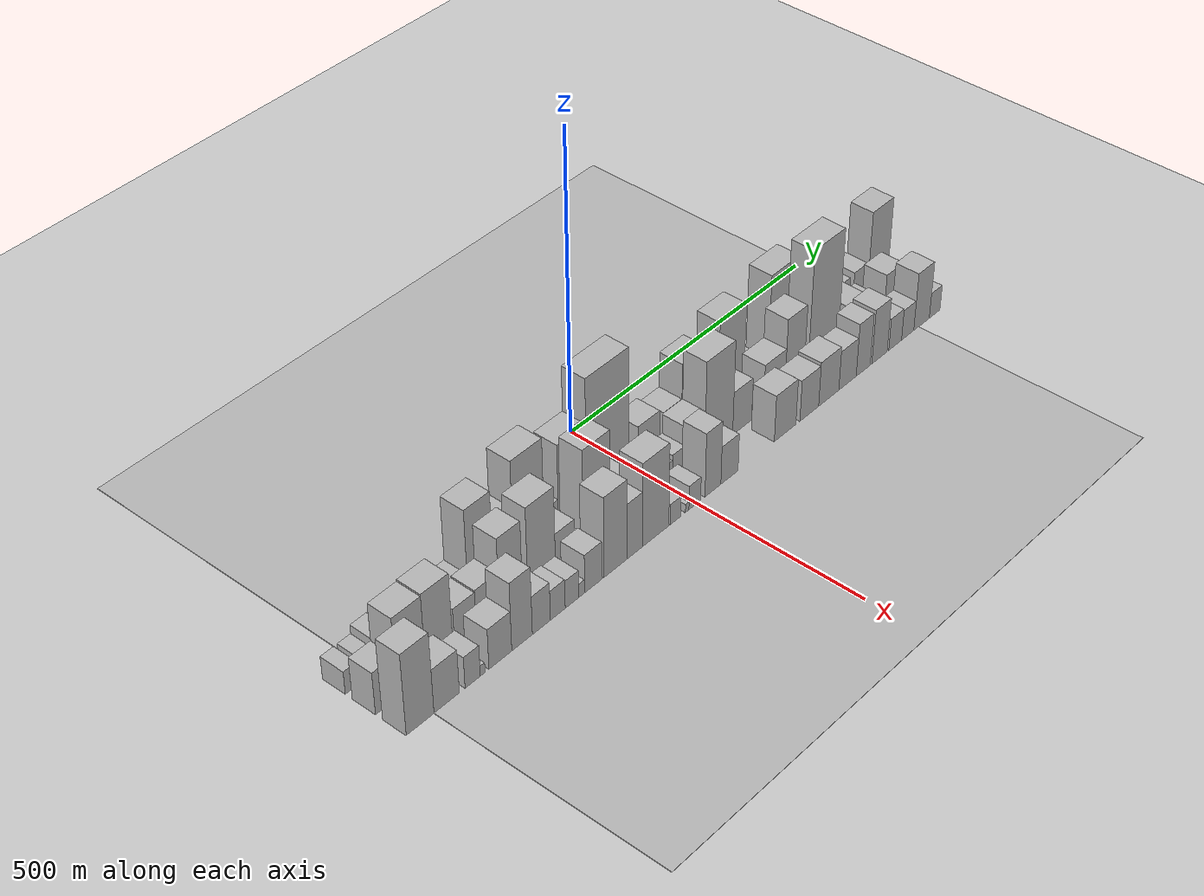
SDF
<?xml version="1.0" encoding="utf-8"?>

<sdf version="1.6">

   <world name="default">

      <gui fullscreen="0">

         <camera name="user_camera">

            <pose>-15 0 4.57585 0 0 0</pose>

            <view_controller>orbit</view_controller>

         </camera>

      </gui>

      <scene>

         <sky>

           <clouds>

             <speed>12</speed>

           </clouds>

         </sky>

         <ambient>0.4 0.4 0.4 1</ambient>

         <background>0.7 0.7 0.7 1</background>

         <shadows>1</shadows>

      </scene>

      <gravity>0 0 -9.8066</gravity>

      <magnetic_field>6e-06 2.3e-05 -4.2e-05</magnetic_field>

      <physics default="0" name="default_physics" type="ode">

         <ode>

            <solver>

               <type>quick</type>

               <iters>10</iters>

               <sor>1.0</sor>

               <use_dynamic_moi_rescaling>0</use_dynamic_moi_rescaling>

            </solver>

            <constraints>

               <cfm>0</cfm>

               <erp>0.2</erp>

               <contact_max_correcting_vel>100</contact_max_correcting_vel>

               <contact_surface_layer>0.001</contact_surface_layer>

            </constraints>

         </ode>

         <max_step_size>0.004</max_step_size>

         <real_time_factor>1</real_time_factor>

         <real_time_update_rate>250</real_time_update_rate>

      </physics>

      <light name="sun" type="directional">

         <cast_shadows>1</cast_shadows>

         <pose>0 0 10 0 0 0</pose>

         <diffuse>0.8 0.8 0.8 1</diffuse>

         <specular>0.2 0.2 0.2 1</specular>

         <attenuation>

            <range>1000</range>

            <constant>0.9</constant>

            <linear>0.01</linear>

            <quadratic>0.001</quadratic>

         </attenuation>

         <direction>-0.5 0.1 -0.9</direction>

      </light>

      <include>

         <name>ground_plane_1</name>

         <uri>model://HANNAS_ground_plane</uri>

         <pose>0 0 0  0 0 0</pose>

      </include>

      <include>

         <name>ground_plane_2</name>

         <uri>model://HANNAS_ground_plane</uri>

         <pose>100 0 0  0 0 0</pose>

      </include>

      <model name="building_1">

         <static>1</static>

         <pose frame="">100.0000 -536.5095 0 0.000000 0.000000 0.000000</pose>

         <link name="link">

            <pose frame="">0 0 19.50 0 0 0</pose>

            <collision name="collision">

               <geometry>

                  <box>

                     <size>40.0000 22.9811 39.0000</size>

                  </box>

               </geometry>

               <max_contacts>10</max_contacts>

               <surface>

                  <contact>

                     <ode/>

                  </contact>

                  <bounce/>

                  <friction>

                     <torsional>

                        <ode/>

                     </torsional>

                     <ode/>

                  </friction>

               </surface>

            </collision>

            <visual name="visual">

               <cast_shadows>0</cast_shadows>

               <geometry>

                  <box>

                     <size>40.0000 22.9811 39.0000</size>

                  </box>

               </geometry>

               <material>

                  <script>

                     <uri>model://HANNAS_wall/materials/scripts</uri>

                     <uri>model://HANNAS_wall/materials/textures</uri>

                     <name>vrc/HANNAS_wall</name>

                  </script>

               </material>

            </visual>

            <self_collide>0</self_collide>

            <enable_wind>0</enable_wind>

            <kinematic>0</kinematic>

         </link>

      </model>

      <model name="building_2">

         <static>1</static>

         <pose frame="">100.0000 -507.4203 0 0.000000 0.000000 0.000000</pose>

         <link name="link">

            <pose frame="">0 0 19.50 0 0 0</pose>

            <collision name="collision">

               <geometry>

                  <box>

                     <size>40.0000 23.1972 39.0000</size>

                  </box>

               </geometry>

               <max_contacts>10</max_contacts>

               <surface>

                  <contact>

                     <ode/>

                  </contact>

                  <bounce/>

                  <friction>

                     <torsional>

                        <ode/>

                     </torsional>

                     <ode/>

                  </friction>

               </surface>

            </collision>

            <visual name="visual">

               <cast_shadows>0</cast_shadows>

               <geometry>

                  <box>

                     <size>40.0000 23.1972 39.0000</size>

                  </box>

               </geometry>

               <material>

                  <script>

                     <uri>model://HANNAS_wall/materials/scripts</uri>

                     <uri>model://HANNAS_wall/materials/textures</uri>

                     <name>vrc/HANNAS_wall</name>

                  </script>

               </material>

            </visual>

            <self_collide>0</self_collide>

            <enable_wind>0</enable_wind>

            <kinematic>0</kinematic>

         </link>

      </model>

      <model name="building_3">

         <static>1</static>

         <pose frame="">100.0000 -481.5491 0 0.000000 0.000000 0.000000</pose>

         <link name="link">

            <pose frame="">0 0 27.00 0 0 0</pose>

            <collision name="collision">

               <geometry>

                  <box>

                     <size>40.0000 28.5451 54.0000</size>

                  </box>

               </geometry>

               <max_contacts>10</max_contacts>

               <surface>

                  <contact>

                     <ode/>

                  </contact>

                  <bounce/>

                  <friction>

                     <torsional>

                        <ode/>

                     </torsional>

                     <ode/>

                  </friction>

               </surface>

            </collision>

            <visual name="visual">

               <cast_shadows>0</cast_shadows>

               <geometry>

                  <box>

                     <size>40.0000 28.5451 54.0000</size>

                  </box>

               </geometry>

               <material>

                  <script>

                     <uri>model://HANNAS_wall/materials/scripts</uri>

                     <uri>model://HANNAS_wall/materials/textures</uri>

                     <name>vrc/HANNAS_wall</name>

                  </script>

               </material>

            </visual>

            <self_collide>0</self_collide>

            <enable_wind>0</enable_wind>

            <kinematic>0</kinematic>

         </link>

      </model>

      <model name="building_4">

         <static>1</static>

         <pose frame="">100.0000 -455.4664 0 0.000000 0.000000 0.000000</pose>

         <link name="link">

            <pose frame="">0 0 21.00 0 0 0</pose>

            <collision name="collision">

               <geometry>

                  <box>

                     <size>40.0000 23.6202 42.0000</size>

                  </box>

               </geometry>

               <max_contacts>10</max_contacts>

               <surface>

                  <contact>

                     <ode/>

                  </contact>

                  <bounce/>

                  <friction>

                     <torsional>

                        <ode/>

                     </torsional>

                     <ode/>

                  </friction>

               </surface>

            </collision>

            <visual name="visual">

               <cast_shadows>0</cast_shadows>

               <geometry>

                  <box>

                     <size>40.0000 23.6202 42.0000</size>

                  </box>

               </geometry>

               <material>

                  <script>

                     <uri>model://HANNAS_wall/materials/scripts</uri>

                     <uri>model://HANNAS_wall/materials/textures</uri>

                     <name>vrc/HANNAS_wall</name>

                  </script>

               </material>

            </visual>

            <self_collide>0</self_collide>

            <enable_wind>0</enable_wind>

            <kinematic>0</kinematic>

         </link>

      </model>

      <model name="building_5">

         <static>1</static>

         <pose frame="">100.0000 -434.0008 0 0.000000 0.000000 0.000000</pose>

         <link name="link">

            <pose frame="">0 0 18.00 0 0 0</pose>

            <collision name="collision">

               <geometry>

                  <box>

                     <size>40.0000 19.3112 36.0000</size>

                  </box>

               </geometry>

               <max_contacts>10</max_contacts>

               <surface>

                  <contact>

                     <ode/>

                  </contact>

                  <bounce/>

                  <friction>

                     <torsional>

                        <ode/>

                     </torsional>

                     <ode/>

                  </friction>

               </surface>

            </collision>

            <visual name="visual">

               <cast_shadows>0</cast_shadows>

               <geometry>

                  <box>

                     <size>40.0000 19.3112 36.0000</size>

                  </box>

               </geometry>

               <material>

                  <script>

                     <uri>model://HANNAS_wall/materials/scripts</uri>

                     <uri>model://HANNAS_wall/materials/textures</uri>

                     <name>vrc/HANNAS_wall</name>

                  </script>

               </material>

            </visual>

            <self_collide>0</self_collide>

            <enable_wind>0</enable_wind>

            <kinematic>0</kinematic>

         </link>

      </model>

      <model name="building_6">

         <static>1</static>

         <pose frame="">100.0000 -419.4309 0 0.000000 0.000000 0.000000</pose>

         <link name="link">

            <pose frame="">0 0 12.00 0 0 0</pose>

            <collision name="collision">

               <geometry>

                  <box>

                     <size>40.0000 9.8286 24.0000</size>

                  </box>

               </geometry>

               <max_contacts>10</max_contacts>

               <surface>

                  <contact>

                     <ode/>

                  </contact>

                  <bounce/>

                  <friction>

                     <torsional>

                        <ode/>

                     </torsional>

                     <ode/>

                  </friction>

               </surface>

            </collision>

            <visual name="visual">

               <cast_shadows>0</cast_shadows>

               <geometry>

                  <box>

                     <size>40.0000 9.8286 24.0000</size>

                  </box>

               </geometry>

               <material>

                  <script>

                     <uri>model://HANNAS_wall/materials/scripts</uri>

                     <uri>model://HANNAS_wall/materials/textures</uri>

                     <name>vrc/HANNAS_wall</name>

                  </script>

               </material>

            </visual>

            <self_collide>0</self_collide>

            <enable_wind>0</enable_wind>

            <kinematic>0</kinematic>

         </link>

      </model>

      <model name="building_7">

         <static>1</static>

         <pose frame="">100.0000 -385.9713 0 0.000000 0.000000 0.000000</pose>

         <link name="link">

            <pose frame="">0 0 33.00 0 0 0</pose>

            <collision name="collision">

               <geometry>

                  <box>

                     <size>40.0000 39.0905 66.0000</size>

                  </box>

               </geometry>

               <max_contacts>10</max_contacts>

               <surface>

                  <contact>

                     <ode/>

                  </contact>

                  <bounce/>

                  <friction>

                     <torsional>

                        <ode/>

                     </torsional>

                     <ode/>

                  </friction>

               </surface>

            </collision>

            <visual name="visual">

               <cast_shadows>0</cast_shadows>

               <geometry>

                  <box>

                     <size>40.0000 39.0905 66.0000</size>

                  </box>

               </geometry>

               <material>

                  <script>

                     <uri>model://HANNAS_wall/materials/scripts</uri>

                     <uri>model://HANNAS_wall/materials/textures</uri>

                     <name>vrc/HANNAS_wall</name>

                  </script>

               </material>

            </visual>

            <self_collide>0</self_collide>

            <enable_wind>0</enable_wind>

            <kinematic>0</kinematic>

         </link>

      </model>

      <model name="building_8">

         <static>1</static>

         <pose frame="">100.0000 -359.7525 0 0.000000 0.000000 0.000000</pose>

         <link name="link">

            <pose frame="">0 0 13.50 0 0 0</pose>

            <collision name="collision">

               <geometry>

                  <box>

                     <size>40.0000 13.3472 27.0000</size>

                  </box>

               </geometry>

               <max_contacts>10</max_contacts>

               <surface>

                  <contact>

                     <ode/>

                  </contact>

                  <bounce/>

                  <friction>

                     <torsional>

                        <ode/>

                     </torsional>

                     <ode/>

                  </friction>

               </surface>

            </collision>

            <visual name="visual">

               <cast_shadows>0</cast_shadows>

               <geometry>

                  <box>

                     <size>40.0000 13.3472 27.0000</size>

                  </box>

               </geometry>

               <material>

                  <script>

                     <uri>model://HANNAS_wall/materials/scripts</uri>

                     <uri>model://HANNAS_wall/materials/textures</uri>

                     <name>vrc/HANNAS_wall</name>

                  </script>

               </material>

            </visual>

            <self_collide>0</self_collide>

            <enable_wind>0</enable_wind>

            <kinematic>0</kinematic>

         </link>

      </model>

      <model name="building_9">

         <static>1</static>

         <pose frame="">100.0000 -341.7140 0 0.000000 0.000000 0.000000</pose>

         <link name="link">

            <pose frame="">0 0 22.50 0 0 0</pose>

            <collision name="collision">

               <geometry>

                  <box>

                     <size>40.0000 22.7298 45.0000</size>

                  </box>

               </geometry>

               <max_contacts>10</max_contacts>

               <surface>

                  <contact>

                     <ode/>

                  </contact>

                  <bounce/>

                  <friction>

                     <torsional>

                        <ode/>

                     </torsional>

                     <ode/>

                  </friction>

               </surface>

            </collision>

            <visual name="visual">

               <cast_shadows>0</cast_shadows>

               <geometry>

                  <box>

                     <size>40.0000 22.7298 45.0000</size>

                  </box>

               </geometry>

               <material>

                  <script>

                     <uri>model://HANNAS_wall/materials/scripts</uri>

                     <uri>model://HANNAS_wall/materials/textures</uri>

                     <name>vrc/HANNAS_wall</name>

                  </script>

               </material>

            </visual>

            <self_collide>0</self_collide>

            <enable_wind>0</enable_wind>

            <kinematic>0</kinematic>

         </link>

      </model>

      <model name="building_10">

         <static>1</static>

         <pose frame="">100.0000 -306.9536 0 0.000000 0.000000 0.000000</pose>

         <link name="link">

            <pose frame="">0 0 76.50 0 0 0</pose>

            <collision name="collision">

               <geometry>

                  <box>

                     <size>40.0000 46.7910 153.0000</size>

                  </box>

               </geometry>

               <max_contacts>10</max_contacts>

               <surface>

                  <contact>

                     <ode/>

                  </contact>

                  <bounce/>

                  <friction>

                     <torsional>

                        <ode/>

                     </torsional>

                     <ode/>

                  </friction>

               </surface>

            </collision>

            <visual name="visual">

               <cast_shadows>0</cast_shadows>

               <geometry>

                  <box>

                     <size>40.0000 46.7910 153.0000</size>

                  </box>

               </geometry>

               <material>

                  <script>

                     <uri>model://HANNAS_wall/materials/scripts</uri>

                     <uri>model://HANNAS_wall/materials/textures</uri>

                     <name>vrc/HANNAS_wall</name>

                  </script>

               </material>

            </visual>

            <self_collide>0</self_collide>

            <enable_wind>0</enable_wind>

            <kinematic>0</kinematic>

         </link>

      </model>

      <model name="building_11">

         <static>1</static>

         <pose frame="">100.0000 -264.3892 0 0.000000 0.000000 0.000000</pose>

         <link name="link">

            <pose frame="">0 0 49.50 0 0 0</pose>

            <collision name="collision">

               <geometry>

                  <box>

                     <size>40.0000 38.3377 99.0000</size>

                  </box>

               </geometry>

               <max_contacts>10</max_contacts>

               <surface>

                  <contact>

                     <ode/>

                  </contact>

                  <bounce/>

                  <friction>

                     <torsional>

                        <ode/>

                     </torsional>

                     <ode/>

                  </friction>

               </surface>

            </collision>

            <visual name="visual">

               <cast_shadows>0</cast_shadows>

               <geometry>

                  <box>

                     <size>40.0000 38.3377 99.0000</size>

                  </box>

               </geometry>

               <material>

                  <script>

                     <uri>model://HANNAS_wall/materials/scripts</uri>

                     <uri>model://HANNAS_wall/materials/textures</uri>

                     <name>vrc/HANNAS_wall</name>

                  </script>

               </material>

            </visual>

            <self_collide>0</self_collide>

            <enable_wind>0</enable_wind>

            <kinematic>0</kinematic>

         </link>

      </model>

      <model name="building_12">

         <static>1</static>

         <pose frame="">100.0000 -215.9052 0 0.000000 0.000000 0.000000</pose>

         <link name="link">

            <pose frame="">0 0 88.50 0 0 0</pose>

            <collision name="collision">

               <geometry>

                  <box>

                     <size>40.0000 58.6303 177.0000</size>

                  </box>

               </geometry>

               <max_contacts>10</max_contacts>

               <surface>

                  <contact>

                     <ode/>

                  </contact>

                  <bounce/>

                  <friction>

                     <torsional>

                        <ode/>

                     </torsional>

                     <ode/>

                  </friction>

               </surface>

            </collision>

            <visual name="visual">

               <cast_shadows>0</cast_shadows>

               <geometry>

                  <box>

                     <size>40.0000 58.6303 177.0000</size>

                  </box>

               </geometry>

               <material>

                  <script>

                     <uri>model://HANNAS_wall/materials/scripts</uri>

                     <uri>model://HANNAS_wall/materials/textures</uri>

                     <name>vrc/HANNAS_wall</name>

                  </script>

               </material>

            </visual>

            <self_collide>0</self_collide>

            <enable_wind>0</enable_wind>

            <kinematic>0</kinematic>

         </link>

      </model>

      <model name="building_13">

         <static>1</static>

         <pose frame="">100.0000 -172.7596 0 0.000000 0.000000 0.000000</pose>

         <link name="link">

            <pose frame="">0 0 27.00 0 0 0</pose>

            <collision name="collision">

               <geometry>

                  <box>

                     <size>40.0000 27.6609 54.0000</size>

                  </box>

               </geometry>

               <max_contacts>10</max_contacts>

               <surface>

                  <contact>

                     <ode/>

                  </contact>

                  <bounce/>

                  <friction>

                     <torsional>

                        <ode/>

                     </torsional>

                     <ode/>

                  </friction>

               </surface>

            </collision>

            <visual name="visual">

               <cast_shadows>0</cast_shadows>

               <geometry>

                  <box>

                     <size>40.0000 27.6609 54.0000</size>

                  </box>

               </geometry>

               <material>

                  <script>

                     <uri>model://HANNAS_wall/materials/scripts</uri>

                     <uri>model://HANNAS_wall/materials/textures</uri>

                     <name>vrc/HANNAS_wall</name>

                  </script>

               </material>

            </visual>

            <self_collide>0</self_collide>

            <enable_wind>0</enable_wind>

            <kinematic>0</kinematic>

         </link>

      </model>

      <model name="building_14">

         <static>1</static>

         <pose frame="">100.0000 -131.3797 0 0.000000 0.000000 0.000000</pose>

         <link name="link">

            <pose frame="">0 0 73.50 0 0 0</pose>

            <collision name="collision">

               <geometry>

                  <box>

                     <size>40.0000 55.0989 147.0000</size>

                  </box>

               </geometry>

               <max_contacts>10</max_contacts>

               <surface>

                  <contact>

                     <ode/>

                  </contact>

                  <bounce/>

                  <friction>

                     <torsional>

                        <ode/>

                     </torsional>

                     <ode/>

                  </friction>

               </surface>

            </collision>

            <visual name="visual">

               <cast_shadows>0</cast_shadows>

               <geometry>

                  <box>

                     <size>40.0000 55.0989 147.0000</size>

                  </box>

               </geometry>

               <material>

                  <script>

                     <uri>model://HANNAS_wall/materials/scripts</uri>

                     <uri>model://HANNAS_wall/materials/textures</uri>

                     <name>vrc/HANNAS_wall</name>

                  </script>

               </material>

            </visual>

            <self_collide>0</self_collide>

            <enable_wind>0</enable_wind>

            <kinematic>0</kinematic>

         </link>

      </model>

      <model name="building_15">

         <static>1</static>

         <pose frame="">100.0000 -61.2850 0 0.000000 0.000000 0.000000</pose>

         <link name="link">

            <pose frame="">0 0 111.00 0 0 0</pose>

            <collision name="collision">

               <geometry>

                  <box>

                     <size>40.0000 85.0905 222.0000</size>

                  </box>

               </geometry>

               <max_contacts>10</max_contacts>

               <surface>

                  <contact>

                     <ode/>

                  </contact>

                  <bounce/>

                  <friction>

                     <torsional>

                        <ode/>

                     </torsional>

                     <ode/>

                  </friction>

               </surface>

            </collision>

            <visual name="visual">

               <cast_shadows>0</cast_shadows>

               <geometry>

                  <box>

                     <size>40.0000 85.0905 222.0000</size>

                  </box>

               </geometry>

               <material>

                  <script>

                     <uri>model://HANNAS_wall/materials/scripts</uri>

                     <uri>model://HANNAS_wall/materials/textures</uri>

                     <name>vrc/HANNAS_wall</name>

                  </script>

               </material>

            </visual>

            <self_collide>0</self_collide>

            <enable_wind>0</enable_wind>

            <kinematic>0</kinematic>

         </link>

      </model>

      <model name="building_16">

         <static>1</static>

         <pose frame="">100.0000 -14.3181 0 0.000000 0.000000 0.000000</pose>

         <link name="link">

            <pose frame="">0 0 10.50 0 0 0</pose>

            <collision name="collision">

               <geometry>

                  <box>

                     <size>40.0000 8.8434 21.0000</size>

                  </box>

               </geometry>

               <max_contacts>10</max_contacts>

               <surface>

                  <contact>

                     <ode/>

                  </contact>

                  <bounce/>

                  <friction>

                     <torsional>

                        <ode/>

                     </torsional>

                     <ode/>

                  </friction>

               </surface>

            </collision>

            <visual name="visual">

               <cast_shadows>0</cast_shadows>

               <geometry>

                  <box>

                     <size>40.0000 8.8434 21.0000</size>

                  </box>

               </geometry>

               <material>

                  <script>

                     <uri>model://HANNAS_wall/materials/scripts</uri>

                     <uri>model://HANNAS_wall/materials/textures</uri>

                     <name>vrc/HANNAS_wall</name>

                  </script>

               </material>

            </visual>

            <self_collide>0</self_collide>

            <enable_wind>0</enable_wind>

            <kinematic>0</kinematic>

         </link>

      </model>

      <model name="building_17">

         <static>1</static>

         <pose frame="">100.0000 22.5195 0 0.000000 0.000000 0.000000</pose>

         <link name="link">

            <pose frame="">0 0 37.50 0 0 0</pose>

            <collision name="collision">

               <geometry>

                  <box>

                     <size>40.0000 44.8317 75.0000</size>

                  </box>

               </geometry>

               <max_contacts>10</max_contacts>

               <surface>

                  <contact>

                     <ode/>

                  </contact>

                  <bounce/>

                  <friction>

                     <torsional>

                        <ode/>

                     </torsional>

                     <ode/>

                  </friction>

               </surface>

            </collision>

            <visual name="visual">

               <cast_shadows>0</cast_shadows>

               <geometry>

                  <box>

                     <size>40.0000 44.8317 75.0000</size>

                  </box>

               </geometry>

               <material>

                  <script>

                     <uri>model://HANNAS_wall/materials/scripts</uri>

                     <uri>model://HANNAS_wall/materials/textures</uri>

                     <name>vrc/HANNAS_wall</name>

                  </script>

               </material>

            </visual>

            <self_collide>0</self_collide>

            <enable_wind>0</enable_wind>

            <kinematic>0</kinematic>

         </link>

      </model>

      <model name="building_18">

         <static>1</static>

         <pose frame="">100.0000 72.0414 0 0.000000 0.000000 0.000000</pose>

         <link name="link">

            <pose frame="">0 0 33.00 0 0 0</pose>

            <collision name="collision">

               <geometry>

                  <box>

                     <size>40.0000 38.2121 66.0000</size>

                  </box>

               </geometry>

               <max_contacts>10</max_contacts>

               <surface>

                  <contact>

                     <ode/>

                  </contact>

                  <bounce/>

                  <friction>

                     <torsional>

                        <ode/>

                     </torsional>

                     <ode/>

                  </friction>

               </surface>

            </collision>

            <visual name="visual">

               <cast_shadows>0</cast_shadows>

               <geometry>

                  <box>

                     <size>40.0000 38.2121 66.0000</size>

                  </box>

               </geometry>

               <material>

                  <script>

                     <uri>model://HANNAS_wall/materials/scripts</uri>

                     <uri>model://HANNAS_wall/materials/textures</uri>

                     <name>vrc/HANNAS_wall</name>

                  </script>

               </material>

            </visual>

            <self_collide>0</self_collide>

            <enable_wind>0</enable_wind>

            <kinematic>0</kinematic>

         </link>

      </model>

      <model name="building_19">

         <static>1</static>

         <pose frame="">100.0000 116.2036 0 0.000000 0.000000 0.000000</pose>

         <link name="link">

            <pose frame="">0 0 63.00 0 0 0</pose>

            <collision name="collision">

               <geometry>

                  <box>

                     <size>40.0000 50.1124 126.0000</size>

                  </box>

               </geometry>

               <max_contacts>10</max_contacts>

               <surface>

                  <contact>

                     <ode/>

                  </contact>

                  <bounce/>

                  <friction>

                     <torsional>

                        <ode/>

                     </torsional>

                     <ode/>

                  </friction>

               </surface>

            </collision>

            <visual name="visual">

               <cast_shadows>0</cast_shadows>

               <geometry>

                  <box>

                     <size>40.0000 50.1124 126.0000</size>

                  </box>

               </geometry>

               <material>

                  <script>

                     <uri>model://HANNAS_wall/materials/scripts</uri>

                     <uri>model://HANNAS_wall/materials/textures</uri>

                     <name>vrc/HANNAS_wall</name>

                  </script>

               </material>

            </visual>

            <self_collide>0</self_collide>

            <enable_wind>0</enable_wind>

            <kinematic>0</kinematic>

         </link>

      </model>

      <model name="building_20">

         <static>1</static>

         <pose frame="">100.0000 155.5497 0 0.000000 0.000000 0.000000</pose>

         <link name="link">

            <pose frame="">0 0 28.50 0 0 0</pose>

            <collision name="collision">

               <geometry>

                  <box>

                     <size>40.0000 28.5797 57.0000</size>

                  </box>

               </geometry>

               <max_contacts>10</max_contacts>

               <surface>

                  <contact>

                     <ode/>

                  </contact>

                  <bounce/>

                  <friction>

                     <torsional>

                        <ode/>

                     </torsional>

                     <ode/>

                  </friction>

               </surface>

            </collision>

            <visual name="visual">

               <cast_shadows>0</cast_shadows>

               <geometry>

                  <box>

                     <size>40.0000 28.5797 57.0000</size>

                  </box>

               </geometry>

               <material>

                  <script>

                     <uri>model://HANNAS_wall/materials/scripts</uri>

                     <uri>model://HANNAS_wall/materials/textures</uri>

                     <name>vrc/HANNAS_wall</name>

                  </script>

               </material>

            </visual>

            <self_collide>0</self_collide>

            <enable_wind>0</enable_wind>

            <kinematic>0</kinematic>

         </link>

      </model>

      <model name="building_21">

         <static>1</static>

         <pose frame="">100.0000 198.1445 0 0.000000 0.000000 0.000000</pose>

         <link name="link">

            <pose frame="">0 0 75.00 0 0 0</pose>

            <collision name="collision">

               <geometry>

                  <box>

                     <size>40.0000 56.6098 150.0000</size>

                  </box>

               </geometry>

               <max_contacts>10</max_contacts>

               <surface>

                  <contact>

                     <ode/>

                  </contact>

                  <bounce/>

                  <friction>

                     <torsional>

                        <ode/>

                     </torsional>

                     <ode/>

                  </friction>

               </surface>

            </collision>

            <visual name="visual">

               <cast_shadows>0</cast_shadows>

               <geometry>

                  <box>

                     <size>40.0000 56.6098 150.0000</size>

                  </box>

               </geometry>

               <material>

                  <script>

                     <uri>model://HANNAS_wall/materials/scripts</uri>

                     <uri>model://HANNAS_wall/materials/textures</uri>

                     <name>vrc/HANNAS_wall</name>

                  </script>

               </material>

            </visual>

            <self_collide>0</self_collide>

            <enable_wind>0</enable_wind>

            <kinematic>0</kinematic>

         </link>

      </model>

      <model name="building_22">

         <static>1</static>

         <pose frame="">100.0000 236.2842 0 0.000000 0.000000 0.000000</pose>

         <link name="link">

            <pose frame="">0 0 19.50 0 0 0</pose>

            <collision name="collision">

               <geometry>

                  <box>

                     <size>40.0000 19.6696 39.0000</size>

                  </box>

               </geometry>

               <max_contacts>10</max_contacts>

               <surface>

                  <contact>

                     <ode/>

                  </contact>

                  <bounce/>

                  <friction>

                     <torsional>

                        <ode/>

                     </torsional>

                     <ode/>

                  </friction>

               </surface>

            </collision>

            <visual name="visual">

               <cast_shadows>0</cast_shadows>

               <geometry>

                  <box>

                     <size>40.0000 19.6696 39.0000</size>

                  </box>

               </geometry>

               <material>

                  <script>

                     <uri>model://HANNAS_wall/materials/scripts</uri>

                     <uri>model://HANNAS_wall/materials/textures</uri>

                     <name>vrc/HANNAS_wall</name>

                  </script>

               </material>

            </visual>

            <self_collide>0</self_collide>

            <enable_wind>0</enable_wind>

            <kinematic>0</kinematic>

         </link>

      </model>

      <model name="building_23">

         <static>1</static>

         <pose frame="">100.0000 256.1067 0 0.000000 0.000000 0.000000</pose>

         <link name="link">

            <pose frame="">0 0 18.00 0 0 0</pose>

            <collision name="collision">

               <geometry>

                  <box>

                     <size>40.0000 19.9755 36.0000</size>

                  </box>

               </geometry>

               <max_contacts>10</max_contacts>

               <surface>

                  <contact>

                     <ode/>

                  </contact>

                  <bounce/>

                  <friction>

                     <torsional>

                        <ode/>

                     </torsional>

                     <ode/>

                  </friction>

               </surface>

            </collision>

            <visual name="visual">

               <cast_shadows>0</cast_shadows>

               <geometry>

                  <box>

                     <size>40.0000 19.9755 36.0000</size>

                  </box>

               </geometry>

               <material>

                  <script>

                     <uri>model://HANNAS_wall/materials/scripts</uri>

                     <uri>model://HANNAS_wall/materials/textures</uri>

                     <name>vrc/HANNAS_wall</name>

                  </script>

               </material>

            </visual>

            <self_collide>0</self_collide>

            <enable_wind>0</enable_wind>

            <kinematic>0</kinematic>

         </link>

      </model>

      <model name="building_24">

         <static>1</static>

         <pose frame="">100.0000 269.6287 0 0.000000 0.000000 0.000000</pose>

         <link name="link">

            <pose frame="">0 0 7.50 0 0 0</pose>

            <collision name="collision">

               <geometry>

                  <box>

                     <size>40.0000 7.0686 15.0000</size>

                  </box>

               </geometry>

               <max_contacts>10</max_contacts>

               <surface>

                  <contact>

                     <ode/>

                  </contact>

                  <bounce/>

                  <friction>

                     <torsional>

                        <ode/>

                     </torsional>

                     <ode/>

                  </friction>

               </surface>

            </collision>

            <visual name="visual">

               <cast_shadows>0</cast_shadows>

               <geometry>

                  <box>

                     <size>40.0000 7.0686 15.0000</size>

                  </box>

               </geometry>

               <material>

                  <script>

                     <uri>model://HANNAS_wall/materials/scripts</uri>

                     <uri>model://HANNAS_wall/materials/textures</uri>

                     <name>vrc/HANNAS_wall</name>

                  </script>

               </material>

            </visual>

            <self_collide>0</self_collide>

            <enable_wind>0</enable_wind>

            <kinematic>0</kinematic>

         </link>

      </model>

      <model name="building_25">

         <static>1</static>

         <pose frame="">100.0000 312.3558 0 0.000000 0.000000 0.000000</pose>

         <link name="link">

            <pose frame="">0 0 82.50 0 0 0</pose>

            <collision name="collision">

               <geometry>

                  <box>

                     <size>40.0000 62.3855 165.0000</size>

                  </box>

               </geometry>

               <max_contacts>10</max_contacts>

               <surface>

                  <contact>

                     <ode/>

                  </contact>

                  <bounce/>

                  <friction>

                     <torsional>

                        <ode/>

                     </torsional>

                     <ode/>

                  </friction>

               </surface>

            </collision>

            <visual name="visual">

               <cast_shadows>0</cast_shadows>

               <geometry>

                  <box>

                     <size>40.0000 62.3855 165.0000</size>

                  </box>

               </geometry>

               <material>

                  <script>

                     <uri>model://HANNAS_wall/materials/scripts</uri>

                     <uri>model://HANNAS_wall/materials/textures</uri>

                     <name>vrc/HANNAS_wall</name>

                  </script>

               </material>

            </visual>

            <self_collide>0</self_collide>

            <enable_wind>0</enable_wind>

            <kinematic>0</kinematic>

         </link>

      </model>

      <model name="building_26">

         <static>1</static>

         <pose frame="">100.0000 363.2936 0 0.000000 0.000000 0.000000</pose>

         <link name="link">

            <pose frame="">0 0 49.50 0 0 0</pose>

            <collision name="collision">

               <geometry>

                  <box>

                     <size>40.0000 33.4901 99.0000</size>

                  </box>

               </geometry>

               <max_contacts>10</max_contacts>

               <surface>

                  <contact>

                     <ode/>

                  </contact>

                  <bounce/>

                  <friction>

                     <torsional>

                        <ode/>

                     </torsional>

                     <ode/>

                  </friction>

               </surface>

            </collision>

            <visual name="visual">

               <cast_shadows>0</cast_shadows>

               <geometry>

                  <box>

                     <size>40.0000 33.4901 99.0000</size>

                  </box>

               </geometry>

               <material>

                  <script>

                     <uri>model://HANNAS_wall/materials/scripts</uri>

                     <uri>model://HANNAS_wall/materials/textures</uri>

                     <name>vrc/HANNAS_wall</name>

                  </script>

               </material>

            </visual>

            <self_collide>0</self_collide>

            <enable_wind>0</enable_wind>

            <kinematic>0</kinematic>

         </link>

      </model>

      <model name="building_27">

         <static>1</static>

         <pose frame="">100.0000 414.3053 0 0.000000 0.000000 0.000000</pose>

         <link name="link">

            <pose frame="">0 0 43.50 0 0 0</pose>

            <collision name="collision">

               <geometry>

                  <box>

                     <size>40.0000 48.5332 87.0000</size>

                  </box>

               </geometry>

               <max_contacts>10</max_contacts>

               <surface>

                  <contact>

                     <ode/>

                  </contact>

                  <bounce/>

                  <friction>

                     <torsional>

                        <ode/>

                     </torsional>

                     <ode/>

                  </friction>

               </surface>

            </collision>

            <visual name="visual">

               <cast_shadows>0</cast_shadows>

               <geometry>

                  <box>

                     <size>40.0000 48.5332 87.0000</size>

                  </box>

               </geometry>

               <material>

                  <script>

                     <uri>model://HANNAS_wall/materials/scripts</uri>

                     <uri>model://HANNAS_wall/materials/textures</uri>

                     <name>vrc/HANNAS_wall</name>

                  </script>

               </material>

            </visual>

            <self_collide>0</self_collide>

            <enable_wind>0</enable_wind>

            <kinematic>0</kinematic>

         </link>

      </model>

      <model name="building_28">

         <static>1</static>

         <pose frame="">100.0000 454.1151 0 0.000000 0.000000 0.000000</pose>

         <link name="link">

            <pose frame="">0 0 27.00 0 0 0</pose>

            <collision name="collision">

               <geometry>

                  <box>

                     <size>40.0000 31.0865 54.0000</size>

                  </box>

               </geometry>

               <max_contacts>10</max_contacts>

               <surface>

                  <contact>

                     <ode/>

                  </contact>

                  <bounce/>

                  <friction>

                     <torsional>

                        <ode/>

                     </torsional>

                     <ode/>

                  </friction>

               </surface>

            </collision>

            <visual name="visual">

               <cast_shadows>0</cast_shadows>

               <geometry>

                  <box>

                     <size>40.0000 31.0865 54.0000</size>

                  </box>

               </geometry>

               <material>

                  <script>

                     <uri>model://HANNAS_wall/materials/scripts</uri>

                     <uri>model://HANNAS_wall/materials/textures</uri>

                     <name>vrc/HANNAS_wall</name>

                  </script>

               </material>

            </visual>

            <self_collide>0</self_collide>

            <enable_wind>0</enable_wind>

            <kinematic>0</kinematic>

         </link>

      </model>

      <model name="building_29">

         <static>1</static>

         <pose frame="">100.0000 495.5309 0 0.000000 0.000000 0.000000</pose>

         <link name="link">

            <pose frame="">0 0 28.50 0 0 0</pose>

            <collision name="collision">

               <geometry>

                  <box>

                     <size>40.0000 31.7450 57.0000</size>

                  </box>

               </geometry>

               <max_contacts>10</max_contacts>

               <surface>

                  <contact>

                     <ode/>

                  </contact>

                  <bounce/>

                  <friction>

                     <torsional>

                        <ode/>

                     </torsional>

                     <ode/>

                  </friction>

               </surface>

            </collision>

            <visual name="visual">

               <cast_shadows>0</cast_shadows>

               <geometry>

                  <box>

                     <size>40.0000 31.7450 57.0000</size>

                  </box>

               </geometry>

               <material>

                  <script>

                     <uri>model://HANNAS_wall/materials/scripts</uri>

                     <uri>model://HANNAS_wall/materials/textures</uri>

                     <name>vrc/HANNAS_wall</name>

                  </script>

               </material>

            </visual>

            <self_collide>0</self_collide>

            <enable_wind>0</enable_wind>

            <kinematic>0</kinematic>

         </link>

      </model>

      <model name="building_30">

         <static>1</static>

         <pose frame="">100.0000 540.2542 0 0.000000 0.000000 0.000000</pose>

         <link name="link">

            <pose frame="">0 0 72.00 0 0 0</pose>

            <collision name="collision">

               <geometry>

                  <box>

                     <size>40.0000 49.7016 144.0000</size>

                  </box>

               </geometry>

               <max_contacts>10</max_contacts>

               <surface>

                  <contact>

                     <ode/>

                  </contact>

                  <bounce/>

                  <friction>

                     <torsional>

                        <ode/>

                     </torsional>

                     <ode/>

                  </friction>

               </surface>

            </collision>

            <visual name="visual">

               <cast_shadows>0</cast_shadows>

               <geometry>

                  <box>

                     <size>40.0000 49.7016 144.0000</size>

                  </box>

               </geometry>

               <material>

                  <script>

                     <uri>model://HANNAS_wall/materials/scripts</uri>

                     <uri>model://HANNAS_wall/materials/textures</uri>

                     <name>vrc/HANNAS_wall</name>

                  </script>

               </material>

            </visual>

            <self_collide>0</self_collide>

            <enable_wind>0</enable_wind>

            <kinematic>0</kinematic>

         </link>

      </model>

      <model name="building_31">

         <static>1</static>

         <pose frame="">152.0000 -529.0312 0 0.000000 0.000000 0.000000</pose>

         <link name="link">

            <pose frame="">0 0 36.00 0 0 0</pose>

            <collision name="collision">

               <geometry>

                  <box>

                     <size>40.0000 37.9376 72.0000</size>

                  </box>

               </geometry>

               <max_contacts>10</max_contacts>

               <surface>

                  <contact>

                     <ode/>

                  </contact>

                  <bounce/>

                  <friction>

                     <torsional>

                        <ode/>

                     </torsional>

                     <ode/>

                  </friction>

               </surface>

            </collision>

            <visual name="visual">

               <cast_shadows>0</cast_shadows>

               <geometry>

                  <box>

                     <size>40.0000 37.9376 72.0000</size>

                  </box>

               </geometry>

               <material>

                  <script>

                     <uri>model://HANNAS_wall/materials/scripts</uri>

                     <uri>model://HANNAS_wall/materials/textures</uri>

                     <name>vrc/HANNAS_wall</name>

                  </script>

               </material>

            </visual>

            <self_collide>0</self_collide>

            <enable_wind>0</enable_wind>

            <kinematic>0</kinematic>

         </link>

      </model>

      <model name="building_32">

         <static>1</static>

         <pose frame="">152.0000 -485.1667 0 0.000000 0.000000 0.000000</pose>

         <link name="link">

            <pose frame="">0 0 67.50 0 0 0</pose>

            <collision name="collision">

               <geometry>

                  <box>

                     <size>40.0000 49.7913 135.0000</size>

                  </box>

               </geometry>

               <max_contacts>10</max_contacts>

               <surface>

                  <contact>

                     <ode/>

                  </contact>

                  <bounce/>

                  <friction>

                     <torsional>

                        <ode/>

                     </torsional>

                     <ode/>

                  </friction>

               </surface>

            </collision>

            <visual name="visual">

               <cast_shadows>0</cast_shadows>

               <geometry>

                  <box>

                     <size>40.0000 49.7913 135.0000</size>

                  </box>

               </geometry>

               <material>

                  <script>

                     <uri>model://HANNAS_wall/materials/scripts</uri>

                     <uri>model://HANNAS_wall/materials/textures</uri>

                     <name>vrc/HANNAS_wall</name>

                  </script>

               </material>

            </visual>

            <self_collide>0</self_collide>

            <enable_wind>0</enable_wind>

            <kinematic>0</kinematic>

         </link>

      </model>

      <model name="building_33">

         <static>1</static>

         <pose frame="">152.0000 -436.1419 0 0.000000 0.000000 0.000000</pose>

         <link name="link">

            <pose frame="">0 0 69.00 0 0 0</pose>

            <collision name="collision">

               <geometry>

                  <box>

                     <size>40.0000 48.2583 138.0000</size>

                  </box>

               </geometry>

               <max_contacts>10</max_contacts>

               <surface>

                  <contact>

                     <ode/>

                  </contact>

                  <bounce/>

                  <friction>

                     <torsional>

                        <ode/>

                     </torsional>

                     <ode/>

                  </friction>

               </surface>

            </collision>

            <visual name="visual">

               <cast_shadows>0</cast_shadows>

               <geometry>

                  <box>

                     <size>40.0000 48.2583 138.0000</size>

                  </box>

               </geometry>

               <material>

                  <script>

                     <uri>model://HANNAS_wall/materials/scripts</uri>

                     <uri>model://HANNAS_wall/materials/textures</uri>

                     <name>vrc/HANNAS_wall</name>

                  </script>

               </material>

            </visual>

            <self_collide>0</self_collide>

            <enable_wind>0</enable_wind>

            <kinematic>0</kinematic>

         </link>

      </model>

      <model name="building_34">

         <static>1</static>

         <pose frame="">152.0000 -389.4961 0 0.000000 0.000000 0.000000</pose>

         <link name="link">

            <pose frame="">0 0 37.50 0 0 0</pose>

            <collision name="collision">

               <geometry>

                  <box>

                     <size>40.0000 39.0334 75.0000</size>

                  </box>

               </geometry>

               <max_contacts>10</max_contacts>

               <surface>

                  <contact>

                     <ode/>

                  </contact>

                  <bounce/>

                  <friction>

                     <torsional>

                        <ode/>

                     </torsional>

                     <ode/>

                  </friction>

               </surface>

            </collision>

            <visual name="visual">

               <cast_shadows>0</cast_shadows>

               <geometry>

                  <box>

                     <size>40.0000 39.0334 75.0000</size>

                  </box>

               </geometry>

               <material>

                  <script>

                     <uri>model://HANNAS_wall/materials/scripts</uri>

                     <uri>model://HANNAS_wall/materials/textures</uri>

                     <name>vrc/HANNAS_wall</name>

                  </script>

               </material>

            </visual>

            <self_collide>0</self_collide>

            <enable_wind>0</enable_wind>

            <kinematic>0</kinematic>

         </link>

      </model>

      <model name="building_35">

         <static>1</static>

         <pose frame="">152.0000 -348.9275 0 0.000000 0.000000 0.000000</pose>

         <link name="link">

            <pose frame="">0 0 39.00 0 0 0</pose>

            <collision name="collision">

               <geometry>

                  <box>

                     <size>40.0000 42.1038 78.0000</size>

                  </box>

               </geometry>

               <max_contacts>10</max_contacts>

               <surface>

                  <contact>

                     <ode/>

                  </contact>

                  <bounce/>

                  <friction>

                     <torsional>

                        <ode/>

                     </torsional>

                     <ode/>

                  </friction>

               </surface>

            </collision>

            <visual name="visual">

               <cast_shadows>0</cast_shadows>

               <geometry>

                  <box>

                     <size>40.0000 42.1038 78.0000</size>

                  </box>

               </geometry>

               <material>

                  <script>

                     <uri>model://HANNAS_wall/materials/scripts</uri>

                     <uri>model://HANNAS_wall/materials/textures</uri>

                     <name>vrc/HANNAS_wall</name>

                  </script>

               </material>

            </visual>

            <self_collide>0</self_collide>

            <enable_wind>0</enable_wind>

            <kinematic>0</kinematic>

         </link>

      </model>

      <model name="building_36">

         <static>1</static>

         <pose frame="">152.0000 -306.4578 0 0.000000 0.000000 0.000000</pose>

         <link name="link">

            <pose frame="">0 0 67.50 0 0 0</pose>

            <collision name="collision">

               <geometry>

                  <box>

                     <size>40.0000 42.8357 135.0000</size>

                  </box>

               </geometry>

               <max_contacts>10</max_contacts>

               <surface>

                  <contact>

                     <ode/>

                  </contact>

                  <bounce/>

                  <friction>

                     <torsional>

                        <ode/>

                     </torsional>

                     <ode/>

                  </friction>

               </surface>

            </collision>

            <visual name="visual">

               <cast_shadows>0</cast_shadows>

               <geometry>

                  <box>

                     <size>40.0000 42.8357 135.0000</size>

                  </box>

               </geometry>

               <material>

                  <script>

                     <uri>model://HANNAS_wall/materials/scripts</uri>

                     <uri>model://HANNAS_wall/materials/textures</uri>

                     <name>vrc/HANNAS_wall</name>

                  </script>

               </material>

            </visual>

            <self_collide>0</self_collide>

            <enable_wind>0</enable_wind>

            <kinematic>0</kinematic>

         </link>

      </model>

      <model name="building_37">

         <static>1</static>

         <pose frame="">152.0000 -248.8536 0 0.000000 0.000000 0.000000</pose>

         <link name="link">

            <pose frame="">0 0 75.00 0 0 0</pose>

            <collision name="collision">

               <geometry>

                  <box>

                     <size>40.0000 52.3726 150.0000</size>

                  </box>

               </geometry>

               <max_contacts>10</max_contacts>

               <surface>

                  <contact>

                     <ode/>

                  </contact>

                  <bounce/>

                  <friction>

                     <torsional>

                        <ode/>

                     </torsional>

                     <ode/>

                  </friction>

               </surface>

            </collision>

            <visual name="visual">

               <cast_shadows>0</cast_shadows>

               <geometry>

                  <box>

                     <size>40.0000 52.3726 150.0000</size>

                  </box>

               </geometry>

               <material>

                  <script>

                     <uri>model://HANNAS_wall/materials/scripts</uri>

                     <uri>model://HANNAS_wall/materials/textures</uri>

                     <name>vrc/HANNAS_wall</name>

                  </script>

               </material>

            </visual>

            <self_collide>0</self_collide>

            <enable_wind>0</enable_wind>

            <kinematic>0</kinematic>

         </link>

      </model>

      <model name="building_38">

         <static>1</static>

         <pose frame="">152.0000 -204.0726 0 0.000000 0.000000 0.000000</pose>

         <link name="link">

            <pose frame="">0 0 34.50 0 0 0</pose>

            <collision name="collision">

               <geometry>

                  <box>

                     <size>40.0000 37.1896 69.0000</size>

                  </box>

               </geometry>

               <max_contacts>10</max_contacts>

               <surface>

                  <contact>

                     <ode/>

                  </contact>

                  <bounce/>

                  <friction>

                     <torsional>

                        <ode/>

                     </torsional>

                     <ode/>

                  </friction>

               </surface>

            </collision>

            <visual name="visual">

               <cast_shadows>0</cast_shadows>

               <geometry>

                  <box>

                     <size>40.0000 37.1896 69.0000</size>

                  </box>

               </geometry>

               <material>

                  <script>

                     <uri>model://HANNAS_wall/materials/scripts</uri>

                     <uri>model://HANNAS_wall/materials/textures</uri>

                     <name>vrc/HANNAS_wall</name>

                  </script>

               </material>

            </visual>

            <self_collide>0</self_collide>

            <enable_wind>0</enable_wind>

            <kinematic>0</kinematic>

         </link>

      </model>

      <model name="building_39">

         <static>1</static>

         <pose frame="">152.0000 -177.0215 0 0.000000 0.000000 0.000000</pose>

         <link name="link">

            <pose frame="">0 0 16.50 0 0 0</pose>

            <collision name="collision">

               <geometry>

                  <box>

                     <size>40.0000 16.9125 33.0000</size>

                  </box>

               </geometry>

               <max_contacts>10</max_contacts>

               <surface>

                  <contact>

                     <ode/>

                  </contact>

                  <bounce/>

                  <friction>

                     <torsional>

                        <ode/>

                     </torsional>

                     <ode/>

                  </friction>

               </surface>

            </collision>

            <visual name="visual">

               <cast_shadows>0</cast_shadows>

               <geometry>

                  <box>

                     <size>40.0000 16.9125 33.0000</size>

                  </box>

               </geometry>

               <material>

                  <script>

                     <uri>model://HANNAS_wall/materials/scripts</uri>

                     <uri>model://HANNAS_wall/materials/textures</uri>

                     <name>vrc/HANNAS_wall</name>

                  </script>

               </material>

            </visual>

            <self_collide>0</self_collide>

            <enable_wind>0</enable_wind>

            <kinematic>0</kinematic>

         </link>

      </model>

      <model name="building_40">

         <static>1</static>

         <pose frame="">152.0000 -142.2107 0 0.000000 0.000000 0.000000</pose>

         <link name="link">

            <pose frame="">0 0 87.00 0 0 0</pose>

            <collision name="collision">

               <geometry>

                  <box>

                     <size>40.0000 52.7091 174.0000</size>

                  </box>

               </geometry>

               <max_contacts>10</max_contacts>

               <surface>

                  <contact>

                     <ode/>

                  </contact>

                  <bounce/>

                  <friction>

                     <torsional>

                        <ode/>

                     </torsional>

                     <ode/>

                  </friction>

               </surface>

            </collision>

            <visual name="visual">

               <cast_shadows>0</cast_shadows>

               <geometry>

                  <box>

                     <size>40.0000 52.7091 174.0000</size>

                  </box>

               </geometry>

               <material>

                  <script>

                     <uri>model://HANNAS_wall/materials/scripts</uri>

                     <uri>model://HANNAS_wall/materials/textures</uri>

                     <name>vrc/HANNAS_wall</name>

                  </script>

               </material>

            </visual>

            <self_collide>0</self_collide>

            <enable_wind>0</enable_wind>

            <kinematic>0</kinematic>

         </link>

      </model>

      <model name="building_41">

         <static>1</static>

         <pose frame="">152.0000 -89.1204 0 0.000000 0.000000 0.000000</pose>

         <link name="link">

            <pose frame="">0 0 36.00 0 0 0</pose>

            <collision name="collision">

               <geometry>

                  <box>

                     <size>40.0000 41.4715 72.0000</size>

                  </box>

               </geometry>

               <max_contacts>10</max_contacts>

               <surface>

                  <contact>

                     <ode/>

                  </contact>

                  <bounce/>

                  <friction>

                     <torsional>

                        <ode/>

                     </torsional>

                     <ode/>

                  </friction>

               </surface>

            </collision>

            <visual name="visual">

               <cast_shadows>0</cast_shadows>

               <geometry>

                  <box>

                     <size>40.0000 41.4715 72.0000</size>

                  </box>

               </geometry>

               <material>

                  <script>

                     <uri>model://HANNAS_wall/materials/scripts</uri>

                     <uri>model://HANNAS_wall/materials/textures</uri>

                     <name>vrc/HANNAS_wall</name>

                  </script>

               </material>

            </visual>

            <self_collide>0</self_collide>

            <enable_wind>0</enable_wind>

            <kinematic>0</kinematic>

         </link>

      </model>

      <model name="building_42">

         <static>1</static>

         <pose frame="">152.0000 -51.3519 0 0.000000 0.000000 0.000000</pose>

         <link name="link">

            <pose frame="">0 0 15.00 0 0 0</pose>

            <collision name="collision">

               <geometry>

                  <box>

                     <size>40.0000 16.0655 30.0000</size>

                  </box>

               </geometry>

               <max_contacts>10</max_contacts>

               <surface>

                  <contact>

                     <ode/>

                  </contact>

                  <bounce/>

                  <friction>

                     <torsional>

                        <ode/>

                     </torsional>

                     <ode/>

                  </friction>

               </surface>

            </collision>

            <visual name="visual">

               <cast_shadows>0</cast_shadows>

               <geometry>

                  <box>

                     <size>40.0000 16.0655 30.0000</size>

                  </box>

               </geometry>

               <material>

                  <script>

                     <uri>model://HANNAS_wall/materials/scripts</uri>

                     <uri>model://HANNAS_wall/materials/textures</uri>

                     <name>vrc/HANNAS_wall</name>

                  </script>

               </material>

            </visual>

            <self_collide>0</self_collide>

            <enable_wind>0</enable_wind>

            <kinematic>0</kinematic>

         </link>

      </model>

      <model name="building_43">

         <static>1</static>

         <pose frame="">152.0000 -26.7826 0 0.000000 0.000000 0.000000</pose>

         <link name="link">

            <pose frame="">0 0 33.00 0 0 0</pose>

            <collision name="collision">

               <geometry>

                  <box>

                     <size>40.0000 33.0731 66.0000</size>

                  </box>

               </geometry>

               <max_contacts>10</max_contacts>

               <surface>

                  <contact>

                     <ode/>

                  </contact>

                  <bounce/>

                  <friction>

                     <torsional>

                        <ode/>

                     </torsional>

                     <ode/>

                  </friction>

               </surface>

            </collision>

            <visual name="visual">

               <cast_shadows>0</cast_shadows>

               <geometry>

                  <box>

                     <size>40.0000 33.0731 66.0000</size>

                  </box>

               </geometry>

               <material>

                  <script>

                     <uri>model://HANNAS_wall/materials/scripts</uri>

                     <uri>model://HANNAS_wall/materials/textures</uri>

                     <name>vrc/HANNAS_wall</name>

                  </script>

               </material>

            </visual>

            <self_collide>0</self_collide>

            <enable_wind>0</enable_wind>

            <kinematic>0</kinematic>

         </link>

      </model>

      <model name="building_44">

         <static>1</static>

         <pose frame="">152.0000 -0.0204 0 0.000000 0.000000 0.000000</pose>

         <link name="link">

            <pose frame="">0 0 19.50 0 0 0</pose>

            <collision name="collision">

               <geometry>

                  <box>

                     <size>40.0000 20.4511 39.0000</size>

                  </box>

               </geometry>

               <max_contacts>10</max_contacts>

               <surface>

                  <contact>

                     <ode/>

                  </contact>

                  <bounce/>

                  <friction>

                     <torsional>

                        <ode/>

                     </torsional>

                     <ode/>

                  </friction>

               </surface>

            </collision>

            <visual name="visual">

               <cast_shadows>0</cast_shadows>

               <geometry>

                  <box>

                     <size>40.0000 20.4511 39.0000</size>

                  </box>

               </geometry>

               <material>

                  <script>

                     <uri>model://HANNAS_wall/materials/scripts</uri>

                     <uri>model://HANNAS_wall/materials/textures</uri>

                     <name>vrc/HANNAS_wall</name>

                  </script>

               </material>

            </visual>

            <self_collide>0</self_collide>

            <enable_wind>0</enable_wind>

            <kinematic>0</kinematic>

         </link>

      </model>

      <model name="building_45">

         <static>1</static>

         <pose frame="">152.0000 23.0759 0 0.000000 0.000000 0.000000</pose>

         <link name="link">

            <pose frame="">0 0 24.00 0 0 0</pose>

            <collision name="collision">

               <geometry>

                  <box>

                     <size>40.0000 25.7415 48.0000</size>

                  </box>

               </geometry>

               <max_contacts>10</max_contacts>

               <surface>

                  <contact>

                     <ode/>

                  </contact>

                  <bounce/>

                  <friction>

                     <torsional>

                        <ode/>

                     </torsional>

                     <ode/>

                  </friction>

               </surface>

            </collision>

            <visual name="visual">

               <cast_shadows>0</cast_shadows>

               <geometry>

                  <box>

                     <size>40.0000 25.7415 48.0000</size>

                  </box>

               </geometry>

               <material>

                  <script>

                     <uri>model://HANNAS_wall/materials/scripts</uri>

                     <uri>model://HANNAS_wall/materials/textures</uri>

                     <name>vrc/HANNAS_wall</name>

                  </script>

               </material>

            </visual>

            <self_collide>0</self_collide>

            <enable_wind>0</enable_wind>

            <kinematic>0</kinematic>

         </link>

      </model>

      <model name="building_46">

         <static>1</static>

         <pose frame="">152.0000 57.0108 0 0.000000 0.000000 0.000000</pose>

         <link name="link">

            <pose frame="">0 0 40.50 0 0 0</pose>

            <collision name="collision">

               <geometry>

                  <box>

                     <size>40.0000 42.1283 81.0000</size>

                  </box>

               </geometry>

               <max_contacts>10</max_contacts>

               <surface>

                  <contact>

                     <ode/>

                  </contact>

                  <bounce/>

                  <friction>

                     <torsional>

                        <ode/>

                     </torsional>

                     <ode/>

                  </friction>

               </surface>

            </collision>

            <visual name="visual">

               <cast_shadows>0</cast_shadows>

               <geometry>

                  <box>

                     <size>40.0000 42.1283 81.0000</size>

                  </box>

               </geometry>

               <material>

                  <script>

                     <uri>model://HANNAS_wall/materials/scripts</uri>

                     <uri>model://HANNAS_wall/materials/textures</uri>

                     <name>vrc/HANNAS_wall</name>

                  </script>

               </material>

            </visual>

            <self_collide>0</self_collide>

            <enable_wind>0</enable_wind>

            <kinematic>0</kinematic>

         </link>

      </model>

      <model name="building_47">

         <static>1</static>

         <pose frame="">152.0000 108.1943 0 0.000000 0.000000 0.000000</pose>

         <link name="link">

            <pose frame="">0 0 82.50 0 0 0</pose>

            <collision name="collision">

               <geometry>

                  <box>

                     <size>40.0000 60.2388 165.0000</size>

                  </box>

               </geometry>

               <max_contacts>10</max_contacts>

               <surface>

                  <contact>

                     <ode/>

                  </contact>

                  <bounce/>

                  <friction>

                     <torsional>

                        <ode/>

                     </torsional>

                     <ode/>

                  </friction>

               </surface>

            </collision>

            <visual name="visual">

               <cast_shadows>0</cast_shadows>

               <geometry>

                  <box>

                     <size>40.0000 60.2388 165.0000</size>

                  </box>

               </geometry>

               <material>

                  <script>

                     <uri>model://HANNAS_wall/materials/scripts</uri>

                     <uri>model://HANNAS_wall/materials/textures</uri>

                     <name>vrc/HANNAS_wall</name>

                  </script>

               </material>

            </visual>

            <self_collide>0</self_collide>

            <enable_wind>0</enable_wind>

            <kinematic>0</kinematic>

         </link>

      </model>

      <model name="building_48">

         <static>1</static>

         <pose frame="">152.0000 158.9577 0 0.000000 0.000000 0.000000</pose>

         <link name="link">

            <pose frame="">0 0 37.50 0 0 0</pose>

            <collision name="collision">

               <geometry>

                  <box>

                     <size>40.0000 41.2879 75.0000</size>

                  </box>

               </geometry>

               <max_contacts>10</max_contacts>

               <surface>

                  <contact>

                     <ode/>

                  </contact>

                  <bounce/>

                  <friction>

                     <torsional>

                        <ode/>

                     </torsional>

                     <ode/>

                  </friction>

               </surface>

            </collision>

            <visual name="visual">

               <cast_shadows>0</cast_shadows>

               <geometry>

                  <box>

                     <size>40.0000 41.2879 75.0000</size>

                  </box>

               </geometry>

               <material>

                  <script>

                     <uri>model://HANNAS_wall/materials/scripts</uri>

                     <uri>model://HANNAS_wall/materials/textures</uri>

                     <name>vrc/HANNAS_wall</name>

                  </script>

               </material>

            </visual>

            <self_collide>0</self_collide>

            <enable_wind>0</enable_wind>

            <kinematic>0</kinematic>

         </link>

      </model>

      <model name="building_49">

         <static>1</static>

         <pose frame="">152.0000 196.6775 0 0.000000 0.000000 0.000000</pose>

         <link name="link">

            <pose frame="">0 0 18.00 0 0 0</pose>

            <collision name="collision">

               <geometry>

                  <box>

                     <size>40.0000 18.1518 36.0000</size>

                  </box>

               </geometry>

               <max_contacts>10</max_contacts>

               <surface>

                  <contact>

                     <ode/>

                  </contact>

                  <bounce/>

                  <friction>

                     <torsional>

                        <ode/>

                     </torsional>

                     <ode/>

                  </friction>

               </surface>

            </collision>

            <visual name="visual">

               <cast_shadows>0</cast_shadows>

               <geometry>

                  <box>

                     <size>40.0000 18.1518 36.0000</size>

                  </box>

               </geometry>

               <material>

                  <script>

                     <uri>model://HANNAS_wall/materials/scripts</uri>

                     <uri>model://HANNAS_wall/materials/textures</uri>

                     <name>vrc/HANNAS_wall</name>

                  </script>

               </material>

            </visual>

            <self_collide>0</self_collide>

            <enable_wind>0</enable_wind>

            <kinematic>0</kinematic>

         </link>

      </model>

      <model name="building_50">

         <static>1</static>

         <pose frame="">152.0000 229.4871 0 0.000000 0.000000 0.000000</pose>

         <link name="link">

            <pose frame="">0 0 40.50 0 0 0</pose>

            <collision name="collision">

               <geometry>

                  <box>

                     <size>40.0000 47.4674 81.0000</size>

                  </box>

               </geometry>

               <max_contacts>10</max_contacts>

               <surface>

                  <contact>

                     <ode/>

                  </contact>

                  <bounce/>

                  <friction>

                     <torsional>

                        <ode/>

                     </torsional>

                     <ode/>

                  </friction>

               </surface>

            </collision>

            <visual name="visual">

               <cast_shadows>0</cast_shadows>

               <geometry>

                  <box>

                     <size>40.0000 47.4674 81.0000</size>

                  </box>

               </geometry>

               <material>

                  <script>

                     <uri>model://HANNAS_wall/materials/scripts</uri>

                     <uri>model://HANNAS_wall/materials/textures</uri>

                     <name>vrc/HANNAS_wall</name>

                  </script>

               </material>

            </visual>

            <self_collide>0</self_collide>

            <enable_wind>0</enable_wind>

            <kinematic>0</kinematic>

         </link>

      </model>

      <model name="building_51">

         <static>1</static>

         <pose frame="">152.0000 274.8759 0 0.000000 0.000000 0.000000</pose>

         <link name="link">

            <pose frame="">0 0 66.00 0 0 0</pose>

            <collision name="collision">

               <geometry>

                  <box>

                     <size>40.0000 43.3102 132.0000</size>

                  </box>

               </geometry>

               <max_contacts>10</max_contacts>

               <surface>

                  <contact>

                     <ode/>

                  </contact>

                  <bounce/>

                  <friction>

                     <torsional>

                        <ode/>

                     </torsional>

                     <ode/>

                  </friction>

               </surface>

            </collision>

            <visual name="visual">

               <cast_shadows>0</cast_shadows>

               <geometry>

                  <box>

                     <size>40.0000 43.3102 132.0000</size>

                  </box>

               </geometry>

               <material>

                  <script>

                     <uri>model://HANNAS_wall/materials/scripts</uri>

                     <uri>model://HANNAS_wall/materials/textures</uri>

                     <name>vrc/HANNAS_wall</name>

                  </script>

               </material>

            </visual>

            <self_collide>0</self_collide>

            <enable_wind>0</enable_wind>

            <kinematic>0</kinematic>

         </link>

      </model>

      <model name="building_52">

         <static>1</static>

         <pose frame="">152.0000 301.0048 0 0.000000 0.000000 0.000000</pose>

         <link name="link">

            <pose frame="">0 0 9.00 0 0 0</pose>

            <collision name="collision">

               <geometry>

                  <box>

                     <size>40.0000 8.9475 18.0000</size>

                  </box>

               </geometry>

               <max_contacts>10</max_contacts>

               <surface>

                  <contact>

                     <ode/>

                  </contact>

                  <bounce/>

                  <friction>

                     <torsional>

                        <ode/>

                     </torsional>

                     <ode/>

                  </friction>

               </surface>

            </collision>

            <visual name="visual">

               <cast_shadows>0</cast_shadows>

               <geometry>

                  <box>

                     <size>40.0000 8.9475 18.0000</size>

                  </box>

               </geometry>

               <material>

                  <script>

                     <uri>model://HANNAS_wall/materials/scripts</uri>

                     <uri>model://HANNAS_wall/materials/textures</uri>

                     <name>vrc/HANNAS_wall</name>

                  </script>

               </material>

            </visual>

            <self_collide>0</self_collide>

            <enable_wind>0</enable_wind>

            <kinematic>0</kinematic>

         </link>

      </model>

      <model name="building_53">

         <static>1</static>

         <pose frame="">152.0000 339.7961 0 0.000000 0.000000 0.000000</pose>

         <link name="link">

            <pose frame="">0 0 109.50 0 0 0</pose>

            <collision name="collision">

               <geometry>

                  <box>

                     <size>40.0000 68.6351 219.0000</size>

                  </box>

               </geometry>

               <max_contacts>10</max_contacts>

               <surface>

                  <contact>

                     <ode/>

                  </contact>

                  <bounce/>

                  <friction>

                     <torsional>

                        <ode/>

                     </torsional>

                     <ode/>

                  </friction>

               </surface>

            </collision>

            <visual name="visual">

               <cast_shadows>0</cast_shadows>

               <geometry>

                  <box>

                     <size>40.0000 68.6351 219.0000</size>

                  </box>

               </geometry>

               <material>

                  <script>

                     <uri>model://HANNAS_wall/materials/scripts</uri>

                     <uri>model://HANNAS_wall/materials/textures</uri>

                     <name>vrc/HANNAS_wall</name>

                  </script>

               </material>

            </visual>

            <self_collide>0</self_collide>

            <enable_wind>0</enable_wind>

            <kinematic>0</kinematic>

         </link>

      </model>

      <model name="building_54">

         <static>1</static>

         <pose frame="">152.0000 380.0673 0 0.000000 0.000000 0.000000</pose>

         <link name="link">

            <pose frame="">0 0 13.50 0 0 0</pose>

            <collision name="collision">

               <geometry>

                  <box>

                     <size>40.0000 11.9073 27.0000</size>

                  </box>

               </geometry>

               <max_contacts>10</max_contacts>

               <surface>

                  <contact>

                     <ode/>

                  </contact>

                  <bounce/>

                  <friction>

                     <torsional>

                        <ode/>

                     </torsional>

                     <ode/>

                  </friction>

               </surface>

            </collision>

            <visual name="visual">

               <cast_shadows>0</cast_shadows>

               <geometry>

                  <box>

                     <size>40.0000 11.9073 27.0000</size>

                  </box>

               </geometry>

               <material>

                  <script>

                     <uri>model://HANNAS_wall/materials/scripts</uri>

                     <uri>model://HANNAS_wall/materials/textures</uri>

                     <name>vrc/HANNAS_wall</name>

                  </script>

               </material>

            </visual>

            <self_collide>0</self_collide>

            <enable_wind>0</enable_wind>

            <kinematic>0</kinematic>

         </link>

      </model>

      <model name="building_55">

         <static>1</static>

         <pose frame="">152.0000 410.9445 0 0.000000 0.000000 0.000000</pose>

         <link name="link">

            <pose frame="">0 0 37.50 0 0 0</pose>

            <collision name="collision">

               <geometry>

                  <box>

                     <size>40.0000 41.8471 75.0000</size>

                  </box>

               </geometry>

               <max_contacts>10</max_contacts>

               <surface>

                  <contact>

                     <ode/>

                  </contact>

                  <bounce/>

                  <friction>

                     <torsional>

                        <ode/>

                     </torsional>

                     <ode/>

                  </friction>

               </surface>

            </collision>

            <visual name="visual">

               <cast_shadows>0</cast_shadows>

               <geometry>

                  <box>

                     <size>40.0000 41.8471 75.0000</size>

                  </box>

               </geometry>

               <material>

                  <script>

                     <uri>model://HANNAS_wall/materials/scripts</uri>

                     <uri>model://HANNAS_wall/materials/textures</uri>

                     <name>vrc/HANNAS_wall</name>

                  </script>

               </material>

            </visual>

            <self_collide>0</self_collide>

            <enable_wind>0</enable_wind>

            <kinematic>0</kinematic>

         </link>

      </model>

      <model name="building_56">

         <static>1</static>

         <pose frame="">152.0000 447.8825 0 0.000000 0.000000 0.000000</pose>

         <link name="link">

            <pose frame="">0 0 27.00 0 0 0</pose>

            <collision name="collision">

               <geometry>

                  <box>

                     <size>40.0000 32.0290 54.0000</size>

                  </box>

               </geometry>

               <max_contacts>10</max_contacts>

               <surface>

                  <contact>

                     <ode/>

                  </contact>

                  <bounce/>

                  <friction>

                     <torsional>

                        <ode/>

                     </torsional>

                     <ode/>

                  </friction>

               </surface>

            </collision>

            <visual name="visual">

               <cast_shadows>0</cast_shadows>

               <geometry>

                  <box>

                     <size>40.0000 32.0290 54.0000</size>

                  </box>

               </geometry>

               <material>

                  <script>

                     <uri>model://HANNAS_wall/materials/scripts</uri>

                     <uri>model://HANNAS_wall/materials/textures</uri>

                     <name>vrc/HANNAS_wall</name>

                  </script>

               </material>

            </visual>

            <self_collide>0</self_collide>

            <enable_wind>0</enable_wind>

            <kinematic>0</kinematic>

         </link>

      </model>

      <model name="building_57">

         <static>1</static>

         <pose frame="">152.0000 472.6197 0 0.000000 0.000000 0.000000</pose>

         <link name="link">

            <pose frame="">0 0 16.50 0 0 0</pose>

            <collision name="collision">

               <geometry>

                  <box>

                     <size>40.0000 17.4455 33.0000</size>

                  </box>

               </geometry>

               <max_contacts>10</max_contacts>

               <surface>

                  <contact>

                     <ode/>

                  </contact>

                  <bounce/>

                  <friction>

                     <torsional>

                        <ode/>

                     </torsional>

                     <ode/>

                  </friction>

               </surface>

            </collision>

            <visual name="visual">

               <cast_shadows>0</cast_shadows>

               <geometry>

                  <box>

                     <size>40.0000 17.4455 33.0000</size>

                  </box>

               </geometry>

               <material>

                  <script>

                     <uri>model://HANNAS_wall/materials/scripts</uri>

                     <uri>model://HANNAS_wall/materials/textures</uri>

                     <name>vrc/HANNAS_wall</name>

                  </script>

               </material>

            </visual>

            <self_collide>0</self_collide>

            <enable_wind>0</enable_wind>

            <kinematic>0</kinematic>

         </link>

      </model>

      <model name="building_58">

         <static>1</static>

         <pose frame="">152.0000 505.5870 0 0.000000 0.000000 0.000000</pose>

         <link name="link">

            <pose frame="">0 0 37.50 0 0 0</pose>

            <collision name="collision">

               <geometry>

                  <box>

                     <size>40.0000 40.4890 75.0000</size>

                  </box>

               </geometry>

               <max_contacts>10</max_contacts>

               <surface>

                  <contact>

                     <ode/>

                  </contact>

                  <bounce/>

                  <friction>

                     <torsional>

                        <ode/>

                     </torsional>

                     <ode/>

                  </friction>

               </surface>

            </collision>

            <visual name="visual">

               <cast_shadows>0</cast_shadows>

               <geometry>

                  <box>

                     <size>40.0000 40.4890 75.0000</size>

                  </box>

               </geometry>

               <material>

                  <script>

                     <uri>model://HANNAS_wall/materials/scripts</uri>

                     <uri>model://HANNAS_wall/materials/textures</uri>

                     <name>vrc/HANNAS_wall</name>

                  </script>

               </material>

            </visual>

            <self_collide>0</self_collide>

            <enable_wind>0</enable_wind>

            <kinematic>0</kinematic>

         </link>

      </model>

      <model name="building_59">

         <static>1</static>

         <pose frame="">152.0000 539.6128 0 0.000000 0.000000 0.000000</pose>

         <link name="link">

            <pose frame="">0 0 15.00 0 0 0</pose>

            <collision name="collision">

               <geometry>

                  <box>

                     <size>40.0000 17.5625 30.0000</size>

                  </box>

               </geometry>

               <max_contacts>10</max_contacts>

               <surface>

                  <contact>

                     <ode/>

                  </contact>

                  <bounce/>

                  <friction>

                     <torsional>

                        <ode/>

                     </torsional>

                     <ode/>

                  </friction>

               </surface>

            </collision>

            <visual name="visual">

               <cast_shadows>0</cast_shadows>

               <geometry>

                  <box>

                     <size>40.0000 17.5625 30.0000</size>

                  </box>

               </geometry>

               <material>

                  <script>

                     <uri>model://HANNAS_wall/materials/scripts</uri>

                     <uri>model://HANNAS_wall/materials/textures</uri>

                     <name>vrc/HANNAS_wall</name>

                  </script>

               </material>

            </visual>

            <self_collide>0</self_collide>

            <enable_wind>0</enable_wind>

            <kinematic>0</kinematic>

         </link>

      </model>

      <model name="building_60">

         <static>1</static>

         <pose frame="">204.0000 -524.0714 0 0.000000 0.000000 0.000000</pose>

         <link name="link">

            <pose frame="">0 0 69.00 0 0 0</pose>

            <collision name="collision">

               <geometry>

                  <box>

                     <size>40.0000 47.8573 138.0000</size>

                  </box>

               </geometry>

               <max_contacts>10</max_contacts>

               <surface>

                  <contact>

                     <ode/>

                  </contact>

                  <bounce/>

                  <friction>

                     <torsional>

                        <ode/>

                     </torsional>

                     <ode/>

                  </friction>

               </surface>

            </collision>

            <visual name="visual">

               <cast_shadows>0</cast_shadows>

               <geometry>

                  <box>

                     <size>40.0000 47.8573 138.0000</size>

                  </box>

               </geometry>

               <material>

                  <script>

                     <uri>model://HANNAS_wall/materials/scripts</uri>

                     <uri>model://HANNAS_wall/materials/textures</uri>

                     <name>vrc/HANNAS_wall</name>

                  </script>

               </material>

            </visual>

            <self_collide>0</self_collide>

            <enable_wind>0</enable_wind>

            <kinematic>0</kinematic>

         </link>

      </model>

      <model name="building_61">

         <static>1</static>

         <pose frame="">204.0000 -477.9115 0 0.000000 0.000000 0.000000</pose>

         <link name="link">

            <pose frame="">0 0 37.50 0 0 0</pose>

            <collision name="collision">

               <geometry>

                  <box>

                     <size>40.0000 44.4625 75.0000</size>

                  </box>

               </geometry>

               <max_contacts>10</max_contacts>

               <surface>

                  <contact>

                     <ode/>

                  </contact>

                  <bounce/>

                  <friction>

                     <torsional>

                        <ode/>

                     </torsional>

                     <ode/>

                  </friction>

               </surface>

            </collision>

            <visual name="visual">

               <cast_shadows>0</cast_shadows>

               <geometry>

                  <box>

                     <size>40.0000 44.4625 75.0000</size>

                  </box>

               </geometry>

               <material>

                  <script>

                     <uri>model://HANNAS_wall/materials/scripts</uri>

                     <uri>model://HANNAS_wall/materials/textures</uri>

                     <name>vrc/HANNAS_wall</name>

                  </script>

               </material>

            </visual>

            <self_collide>0</self_collide>

            <enable_wind>0</enable_wind>

            <kinematic>0</kinematic>

         </link>

      </model>

      <model name="building_62">

         <static>1</static>

         <pose frame="">204.0000 -432.0615 0 0.000000 0.000000 0.000000</pose>

         <link name="link">

            <pose frame="">0 0 27.00 0 0 0</pose>

            <collision name="collision">

               <geometry>

                  <box>

                     <size>40.0000 27.2375 54.0000</size>

                  </box>

               </geometry>

               <max_contacts>10</max_contacts>

               <surface>

                  <contact>

                     <ode/>

                  </contact>

                  <bounce/>

                  <friction>

                     <torsional>

                        <ode/>

                     </torsional>

                     <ode/>

                  </friction>

               </surface>

            </collision>

            <visual name="visual">

               <cast_shadows>0</cast_shadows>

               <geometry>

                  <box>

                     <size>40.0000 27.2375 54.0000</size>

                  </box>

               </geometry>

               <material>

                  <script>

                     <uri>model://HANNAS_wall/materials/scripts</uri>

                     <uri>model://HANNAS_wall/materials/textures</uri>

                     <name>vrc/HANNAS_wall</name>

                  </script>

               </material>

            </visual>

            <self_collide>0</self_collide>

            <enable_wind>0</enable_wind>

            <kinematic>0</kinematic>

         </link>

      </model>

      <model name="building_63">

         <static>1</static>

         <pose frame="">204.0000 -414.2330 0 0.000000 0.000000 0.000000</pose>

         <link name="link">

            <pose frame="">0 0 9.00 0 0 0</pose>

            <collision name="collision">

               <geometry>

                  <box>

                     <size>40.0000 8.4195 18.0000</size>

                  </box>

               </geometry>

               <max_contacts>10</max_contacts>

               <surface>

                  <contact>

                     <ode/>

                  </contact>

                  <bounce/>

                  <friction>

                     <torsional>

                        <ode/>

                     </torsional>

                     <ode/>

                  </friction>

               </surface>

            </collision>

            <visual name="visual">

               <cast_shadows>0</cast_shadows>

               <geometry>

                  <box>

                     <size>40.0000 8.4195 18.0000</size>

                  </box>

               </geometry>

               <material>

                  <script>

                     <uri>model://HANNAS_wall/materials/scripts</uri>

                     <uri>model://HANNAS_wall/materials/textures</uri>

                     <name>vrc/HANNAS_wall</name>

                  </script>

               </material>

            </visual>

            <self_collide>0</self_collide>

            <enable_wind>0</enable_wind>

            <kinematic>0</kinematic>

         </link>

      </model>

      <model name="building_64">

         <static>1</static>

         <pose frame="">204.0000 -382.3311 0 0.000000 0.000000 0.000000</pose>

         <link name="link">

            <pose frame="">0 0 34.50 0 0 0</pose>

            <collision name="collision">

               <geometry>

                  <box>

                     <size>40.0000 41.3843 69.0000</size>

                  </box>

               </geometry>

               <max_contacts>10</max_contacts>

               <surface>

                  <contact>

                     <ode/>

                  </contact>

                  <bounce/>

                  <friction>

                     <torsional>

                        <ode/>

                     </torsional>

                     <ode/>

                  </friction>

               </surface>

            </collision>

            <visual name="visual">

               <cast_shadows>0</cast_shadows>

               <geometry>

                  <box>

                     <size>40.0000 41.3843 69.0000</size>

                  </box>

               </geometry>

               <material>

                  <script>

                     <uri>model://HANNAS_wall/materials/scripts</uri>

                     <uri>model://HANNAS_wall/materials/textures</uri>

                     <name>vrc/HANNAS_wall</name>

                  </script>

               </material>

            </visual>

            <self_collide>0</self_collide>

            <enable_wind>0</enable_wind>

            <kinematic>0</kinematic>

         </link>

      </model>

      <model name="building_65">

         <static>1</static>

         <pose frame="">204.0000 -342.7157 0 0.000000 0.000000 0.000000</pose>

         <link name="link">

            <pose frame="">0 0 58.50 0 0 0</pose>

            <collision name="collision">

               <geometry>

                  <box>

                     <size>40.0000 37.8464 117.0000</size>

                  </box>

               </geometry>

               <max_contacts>10</max_contacts>

               <surface>

                  <contact>

                     <ode/>

                  </contact>

                  <bounce/>

                  <friction>

                     <torsional>

                        <ode/>

                     </torsional>

                     <ode/>

                  </friction>

               </surface>

            </collision>

            <visual name="visual">

               <cast_shadows>0</cast_shadows>

               <geometry>

                  <box>

                     <size>40.0000 37.8464 117.0000</size>

                  </box>

               </geometry>

               <material>

                  <script>

                     <uri>model://HANNAS_wall/materials/scripts</uri>

                     <uri>model://HANNAS_wall/materials/textures</uri>

                     <name>vrc/HANNAS_wall</name>

                  </script>

               </material>

            </visual>

            <self_collide>0</self_collide>

            <enable_wind>0</enable_wind>

            <kinematic>0</kinematic>

         </link>

      </model>

      <model name="building_66">

         <static>1</static>

         <pose frame="">204.0000 -307.0524 0 0.000000 0.000000 0.000000</pose>

         <link name="link">

            <pose frame="">0 0 33.00 0 0 0</pose>

            <collision name="collision">

               <geometry>

                  <box>

                     <size>40.0000 33.4802 66.0000</size>

                  </box>

               </geometry>

               <max_contacts>10</max_contacts>

               <surface>

                  <contact>

                     <ode/>

                  </contact>

                  <bounce/>

                  <friction>

                     <torsional>

                        <ode/>

                     </torsional>

                     <ode/>

                  </friction>

               </surface>

            </collision>

            <visual name="visual">

               <cast_shadows>0</cast_shadows>

               <geometry>

                  <box>

                     <size>40.0000 33.4802 66.0000</size>

                  </box>

               </geometry>

               <material>

                  <script>

                     <uri>model://HANNAS_wall/materials/scripts</uri>

                     <uri>model://HANNAS_wall/materials/textures</uri>

                     <name>vrc/HANNAS_wall</name>

                  </script>

               </material>

            </visual>

            <self_collide>0</self_collide>

            <enable_wind>0</enable_wind>

            <kinematic>0</kinematic>

         </link>

      </model>

      <model name="building_67">

         <static>1</static>

         <pose frame="">204.0000 -276.2774 0 0.000000 0.000000 0.000000</pose>

         <link name="link">

            <pose frame="">0 0 25.50 0 0 0</pose>

            <collision name="collision">

               <geometry>

                  <box>

                     <size>40.0000 28.0697 51.0000</size>

                  </box>

               </geometry>

               <max_contacts>10</max_contacts>

               <surface>

                  <contact>

                     <ode/>

                  </contact>

                  <bounce/>

                  <friction>

                     <torsional>

                        <ode/>

                     </torsional>

                     <ode/>

                  </friction>

               </surface>

            </collision>

            <visual name="visual">

               <cast_shadows>0</cast_shadows>

               <geometry>

                  <box>

                     <size>40.0000 28.0697 51.0000</size>

                  </box>

               </geometry>

               <material>

                  <script>

                     <uri>model://HANNAS_wall/materials/scripts</uri>

                     <uri>model://HANNAS_wall/materials/textures</uri>

                     <name>vrc/HANNAS_wall</name>

                  </script>

               </material>

            </visual>

            <self_collide>0</self_collide>

            <enable_wind>0</enable_wind>

            <kinematic>0</kinematic>

         </link>

      </model>

      <model name="building_68">

         <static>1</static>

         <pose frame="">204.0000 -249.1602 0 0.000000 0.000000 0.000000</pose>

         <link name="link">

            <pose frame="">0 0 24.00 0 0 0</pose>

            <collision name="collision">

               <geometry>

                  <box>

                     <size>40.0000 26.1648 48.0000</size>

                  </box>

               </geometry>

               <max_contacts>10</max_contacts>

               <surface>

                  <contact>

                     <ode/>

                  </contact>

                  <bounce/>

                  <friction>

                     <torsional>

                        <ode/>

                     </torsional>

                     <ode/>

                  </friction>

               </surface>

            </collision>

            <visual name="visual">

               <cast_shadows>0</cast_shadows>

               <geometry>

                  <box>

                     <size>40.0000 26.1648 48.0000</size>

                  </box>

               </geometry>

               <material>

                  <script>

                     <uri>model://HANNAS_wall/materials/scripts</uri>

                     <uri>model://HANNAS_wall/materials/textures</uri>

                     <name>vrc/HANNAS_wall</name>

                  </script>

               </material>

            </visual>

            <self_collide>0</self_collide>

            <enable_wind>0</enable_wind>

            <kinematic>0</kinematic>

         </link>

      </model>

      <model name="building_69">

         <static>1</static>

         <pose frame="">204.0000 -230.5649 0 0.000000 0.000000 0.000000</pose>

         <link name="link">

            <pose frame="">0 0 12.00 0 0 0</pose>

            <collision name="collision">

               <geometry>

                  <box>

                     <size>40.0000 11.0256 24.0000</size>

                  </box>

               </geometry>

               <max_contacts>10</max_contacts>

               <surface>

                  <contact>

                     <ode/>

                  </contact>

                  <bounce/>

                  <friction>

                     <torsional>

                        <ode/>

                     </torsional>

                     <ode/>

                  </friction>

               </surface>

            </collision>

            <visual name="visual">

               <cast_shadows>0</cast_shadows>

               <geometry>

                  <box>

                     <size>40.0000 11.0256 24.0000</size>

                  </box>

               </geometry>

               <material>

                  <script>

                     <uri>model://HANNAS_wall/materials/scripts</uri>

                     <uri>model://HANNAS_wall/materials/textures</uri>

                     <name>vrc/HANNAS_wall</name>

                  </script>

               </material>

            </visual>

            <self_collide>0</self_collide>

            <enable_wind>0</enable_wind>

            <kinematic>0</kinematic>

         </link>

      </model>

      <model name="building_70">

         <static>1</static>

         <pose frame="">204.0000 -208.4554 0 0.000000 0.000000 0.000000</pose>

         <link name="link">

            <pose frame="">0 0 33.00 0 0 0</pose>

            <collision name="collision">

               <geometry>

                  <box>

                     <size>40.0000 33.1934 66.0000</size>

                  </box>

               </geometry>

               <max_contacts>10</max_contacts>

               <surface>

                  <contact>

                     <ode/>

                  </contact>

                  <bounce/>

                  <friction>

                     <torsional>

                        <ode/>

                     </torsional>

                     <ode/>

                  </friction>

               </surface>

            </collision>

            <visual name="visual">

               <cast_shadows>0</cast_shadows>

               <geometry>

                  <box>

                     <size>40.0000 33.1934 66.0000</size>

                  </box>

               </geometry>

               <material>

                  <script>

                     <uri>model://HANNAS_wall/materials/scripts</uri>

                     <uri>model://HANNAS_wall/materials/textures</uri>

                     <name>vrc/HANNAS_wall</name>

                  </script>

               </material>

            </visual>

            <self_collide>0</self_collide>

            <enable_wind>0</enable_wind>

            <kinematic>0</kinematic>

         </link>

      </model>

      <model name="building_71">

         <static>1</static>

         <pose frame="">204.0000 -165.1659 0 0.000000 0.000000 0.000000</pose>

         <link name="link">

            <pose frame="">0 0 69.00 0 0 0</pose>

            <collision name="collision">

               <geometry>

                  <box>

                     <size>40.0000 45.3856 138.0000</size>

                  </box>

               </geometry>

               <max_contacts>10</max_contacts>

               <surface>

                  <contact>

                     <ode/>

                  </contact>

                  <bounce/>

                  <friction>

                     <torsional>

                        <ode/>

                     </torsional>

                     <ode/>

                  </friction>

               </surface>

            </collision>

            <visual name="visual">

               <cast_shadows>0</cast_shadows>

               <geometry>

                  <box>

                     <size>40.0000 45.3856 138.0000</size>

                  </box>

               </geometry>

               <material>

                  <script>

                     <uri>model://HANNAS_wall/materials/scripts</uri>

                     <uri>model://HANNAS_wall/materials/textures</uri>

                     <name>vrc/HANNAS_wall</name>

                  </script>

               </material>

            </visual>

            <self_collide>0</self_collide>

            <enable_wind>0</enable_wind>

            <kinematic>0</kinematic>

         </link>

      </model>

      <model name="building_72">

         <static>1</static>

         <pose frame="">204.0000 -127.1355 0 0.000000 0.000000 0.000000</pose>

         <link name="link">

            <pose frame="">0 0 48.00 0 0 0</pose>

            <collision name="collision">

               <geometry>

                  <box>

                     <size>40.0000 30.6753 96.0000</size>

                  </box>

               </geometry>

               <max_contacts>10</max_contacts>

               <surface>

                  <contact>

                     <ode/>

                  </contact>

                  <bounce/>

                  <friction>

                     <torsional>

                        <ode/>

                     </torsional>

                     <ode/>

                  </friction>

               </surface>

            </collision>

            <visual name="visual">

               <cast_shadows>0</cast_shadows>

               <geometry>

                  <box>

                     <size>40.0000 30.6753 96.0000</size>

                  </box>

               </geometry>

               <material>

                  <script>

                     <uri>model://HANNAS_wall/materials/scripts</uri>

                     <uri>model://HANNAS_wall/materials/textures</uri>

                     <name>vrc/HANNAS_wall</name>

                  </script>

               </material>

            </visual>

            <self_collide>0</self_collide>

            <enable_wind>0</enable_wind>

            <kinematic>0</kinematic>

         </link>

      </model>

      <model name="building_73">

         <static>1</static>

         <pose frame="">204.0000 -85.3646 0 0.000000 0.000000 0.000000</pose>

         <link name="link">

            <pose frame="">0 0 72.00 0 0 0</pose>

            <collision name="collision">

               <geometry>

                  <box>

                     <size>40.0000 52.8665 144.0000</size>

                  </box>

               </geometry>

               <max_contacts>10</max_contacts>

               <surface>

                  <contact>

                     <ode/>

                  </contact>

                  <bounce/>

                  <friction>

                     <torsional>

                        <ode/>

                     </torsional>

                     <ode/>

                  </friction>

               </surface>

            </collision>

            <visual name="visual">

               <cast_shadows>0</cast_shadows>

               <geometry>

                  <box>

                     <size>40.0000 52.8665 144.0000</size>

                  </box>

               </geometry>

               <material>

                  <script>

                     <uri>model://HANNAS_wall/materials/scripts</uri>

                     <uri>model://HANNAS_wall/materials/textures</uri>

                     <name>vrc/HANNAS_wall</name>

                  </script>

               </material>

            </visual>

            <self_collide>0</self_collide>

            <enable_wind>0</enable_wind>

            <kinematic>0</kinematic>

         </link>

      </model>

      <model name="building_74">

         <static>1</static>

         <pose frame="">204.0000 -45.3806 0 0.000000 0.000000 0.000000</pose>

         <link name="link">

            <pose frame="">0 0 18.00 0 0 0</pose>

            <collision name="collision">

               <geometry>

                  <box>

                     <size>40.0000 21.1015 36.0000</size>

                  </box>

               </geometry>

               <max_contacts>10</max_contacts>

               <surface>

                  <contact>

                     <ode/>

                  </contact>

                  <bounce/>

                  <friction>

                     <torsional>

                        <ode/>

                     </torsional>

                     <ode/>

                  </friction>

               </surface>

            </collision>

            <visual name="visual">

               <cast_shadows>0</cast_shadows>

               <geometry>

                  <box>

                     <size>40.0000 21.1015 36.0000</size>

                  </box>

               </geometry>

               <material>

                  <script>

                     <uri>model://HANNAS_wall/materials/scripts</uri>

                     <uri>model://HANNAS_wall/materials/textures</uri>

                     <name>vrc/HANNAS_wall</name>

                  </script>

               </material>

            </visual>

            <self_collide>0</self_collide>

            <enable_wind>0</enable_wind>

            <kinematic>0</kinematic>

         </link>

      </model>

      <model name="building_75">

         <static>1</static>

         <pose frame="">204.0000 -21.2537 0 0.000000 0.000000 0.000000</pose>

         <link name="link">

            <pose frame="">0 0 7.50 0 0 0</pose>

            <collision name="collision">

               <geometry>

                  <box>

                     <size>40.0000 7.1522 15.0000</size>

                  </box>

               </geometry>

               <max_contacts>10</max_contacts>

               <surface>

                  <contact>

                     <ode/>

                  </contact>

                  <bounce/>

                  <friction>

                     <torsional>

                        <ode/>

                     </torsional>

                     <ode/>

                  </friction>

               </surface>

            </collision>

            <visual name="visual">

               <cast_shadows>0</cast_shadows>

               <geometry>

                  <box>

                     <size>40.0000 7.1522 15.0000</size>

                  </box>

               </geometry>

               <material>

                  <script>

                     <uri>model://HANNAS_wall/materials/scripts</uri>

                     <uri>model://HANNAS_wall/materials/textures</uri>

                     <name>vrc/HANNAS_wall</name>

                  </script>

               </material>

            </visual>

            <self_collide>0</self_collide>

            <enable_wind>0</enable_wind>

            <kinematic>0</kinematic>

         </link>

      </model>

      <model name="building_76">

         <static>1</static>

         <pose frame="">204.0000 -5.5008 0 0.000000 0.000000 0.000000</pose>

         <link name="link">

            <pose frame="">0 0 21.00 0 0 0</pose>

            <collision name="collision">

               <geometry>

                  <box>

                     <size>40.0000 24.3536 42.0000</size>

                  </box>

               </geometry>

               <max_contacts>10</max_contacts>

               <surface>

                  <contact>

                     <ode/>

                  </contact>

                  <bounce/>

                  <friction>

                     <torsional>

                        <ode/>

                     </torsional>

                     <ode/>

                  </friction>

               </surface>

            </collision>

            <visual name="visual">

               <cast_shadows>0</cast_shadows>

               <geometry>

                  <box>

                     <size>40.0000 24.3536 42.0000</size>

                  </box>

               </geometry>

               <material>

                  <script>

                     <uri>model://HANNAS_wall/materials/scripts</uri>

                     <uri>model://HANNAS_wall/materials/textures</uri>

                     <name>vrc/HANNAS_wall</name>

                  </script>

               </material>

            </visual>

            <self_collide>0</self_collide>

            <enable_wind>0</enable_wind>

            <kinematic>0</kinematic>

         </link>

      </model>

      <model name="building_77">

         <static>1</static>

         <pose frame="">204.0000 32.3693 0 0.000000 0.000000 0.000000</pose>

         <link name="link">

            <pose frame="">0 0 55.50 0 0 0</pose>

            <collision name="collision">

               <geometry>

                  <box>

                     <size>40.0000 33.3866 111.0000</size>

                  </box>

               </geometry>

               <max_contacts>10</max_contacts>

               <surface>

                  <contact>

                     <ode/>

                  </contact>

                  <bounce/>

                  <friction>

                     <torsional>

                        <ode/>

                     </torsional>

                     <ode/>

                  </friction>

               </surface>

            </collision>

            <visual name="visual">

               <cast_shadows>0</cast_shadows>

               <geometry>

                  <box>

                     <size>40.0000 33.3866 111.0000</size>

                  </box>

               </geometry>

               <material>

                  <script>

                     <uri>model://HANNAS_wall/materials/scripts</uri>

                     <uri>model://HANNAS_wall/materials/textures</uri>

                     <name>vrc/HANNAS_wall</name>

                  </script>

               </material>

            </visual>

            <self_collide>0</self_collide>

            <enable_wind>0</enable_wind>

            <kinematic>0</kinematic>

         </link>

      </model>

      <model name="building_78">

         <static>1</static>

         <pose frame="">204.0000 67.3168 0 0.000000 0.000000 0.000000</pose>

         <link name="link">

            <pose frame="">0 0 33.00 0 0 0</pose>

            <collision name="collision">

               <geometry>

                  <box>

                     <size>40.0000 36.5084 66.0000</size>

                  </box>

               </geometry>

               <max_contacts>10</max_contacts>

               <surface>

                  <contact>

                     <ode/>

                  </contact>

                  <bounce/>

                  <friction>

                     <torsional>

                        <ode/>

                     </torsional>

                     <ode/>

                  </friction>

               </surface>

            </collision>

            <visual name="visual">

               <cast_shadows>0</cast_shadows>

               <geometry>

                  <box>

                     <size>40.0000 36.5084 66.0000</size>

                  </box>

               </geometry>

               <material>

                  <script>

                     <uri>model://HANNAS_wall/materials/scripts</uri>

                     <uri>model://HANNAS_wall/materials/textures</uri>

                     <name>vrc/HANNAS_wall</name>

                  </script>

               </material>

            </visual>

            <self_collide>0</self_collide>

            <enable_wind>0</enable_wind>

            <kinematic>0</kinematic>

         </link>

      </model>

      <model name="building_79">

         <static>1</static>

         <pose frame="">204.0000 188.1586 0 0.000000 0.000000 0.000000</pose>

         <link name="link">

            <pose frame="">0 0 40.50 0 0 0</pose>

            <collision name="collision">

               <geometry>

                  <box>

                     <size>40.0000 47.7251 81.0000</size>

                  </box>

               </geometry>

               <max_contacts>10</max_contacts>

               <surface>

                  <contact>

                     <ode/>

                  </contact>

                  <bounce/>

                  <friction>

                     <torsional>

                        <ode/>

                     </torsional>

                     <ode/>

                  </friction>

               </surface>

            </collision>

            <visual name="visual">

               <cast_shadows>0</cast_shadows>

               <geometry>

                  <box>

                     <size>40.0000 47.7251 81.0000</size>

                  </box>

               </geometry>

               <material>

                  <script>

                     <uri>model://HANNAS_wall/materials/scripts</uri>

                     <uri>model://HANNAS_wall/materials/textures</uri>

                     <name>vrc/HANNAS_wall</name>

                  </script>

               </material>

            </visual>

            <self_collide>0</self_collide>

            <enable_wind>0</enable_wind>

            <kinematic>0</kinematic>

         </link>

      </model>

      <model name="building_80">

         <static>1</static>

         <pose frame="">204.0000 242.1628 0 0.000000 0.000000 0.000000</pose>

         <link name="link">

            <pose frame="">0 0 36.00 0 0 0</pose>

            <collision name="collision">

               <geometry>

                  <box>

                     <size>40.0000 42.2833 72.0000</size>

                  </box>

               </geometry>

               <max_contacts>10</max_contacts>

               <surface>

                  <contact>

                     <ode/>

                  </contact>

                  <bounce/>

                  <friction>

                     <torsional>

                        <ode/>

                     </torsional>

                     <ode/>

                  </friction>

               </surface>

            </collision>

            <visual name="visual">

               <cast_shadows>0</cast_shadows>

               <geometry>

                  <box>

                     <size>40.0000 42.2833 72.0000</size>

                  </box>

               </geometry>

               <material>

                  <script>

                     <uri>model://HANNAS_wall/materials/scripts</uri>

                     <uri>model://HANNAS_wall/materials/textures</uri>

                     <name>vrc/HANNAS_wall</name>

                  </script>

               </material>

            </visual>

            <self_collide>0</self_collide>

            <enable_wind>0</enable_wind>

            <kinematic>0</kinematic>

         </link>

      </model>

      <model name="building_81">

         <static>1</static>

         <pose frame="">204.0000 286.3610 0 0.000000 0.000000 0.000000</pose>

         <link name="link">

            <pose frame="">0 0 39.00 0 0 0</pose>

            <collision name="collision">

               <geometry>

                  <box>

                     <size>40.0000 46.1131 78.0000</size>

                  </box>

               </geometry>

               <max_contacts>10</max_contacts>

               <surface>

                  <contact>

                     <ode/>

                  </contact>

                  <bounce/>

                  <friction>

                     <torsional>

                        <ode/>

                     </torsional>

                     <ode/>

                  </friction>

               </surface>

            </collision>

            <visual name="visual">

               <cast_shadows>0</cast_shadows>

               <geometry>

                  <box>

                     <size>40.0000 46.1131 78.0000</size>

                  </box>

               </geometry>

               <material>

                  <script>

                     <uri>model://HANNAS_wall/materials/scripts</uri>

                     <uri>model://HANNAS_wall/materials/textures</uri>

                     <name>vrc/HANNAS_wall</name>

                  </script>

               </material>

            </visual>

            <self_collide>0</self_collide>

            <enable_wind>0</enable_wind>

            <kinematic>0</kinematic>

         </link>

      </model>

      <model name="building_82">

         <static>1</static>

         <pose frame="">204.0000 329.6056 0 0.000000 0.000000 0.000000</pose>

         <link name="link">

            <pose frame="">0 0 34.50 0 0 0</pose>

            <collision name="collision">

               <geometry>

                  <box>

                     <size>40.0000 40.3760 69.0000</size>

                  </box>

               </geometry>

               <max_contacts>10</max_contacts>

               <surface>

                  <contact>

                     <ode/>

                  </contact>

                  <bounce/>

                  <friction>

                     <torsional>

                        <ode/>

                     </torsional>

                     <ode/>

                  </friction>

               </surface>

            </collision>

            <visual name="visual">

               <cast_shadows>0</cast_shadows>

               <geometry>

                  <box>

                     <size>40.0000 40.3760 69.0000</size>

                  </box>

               </geometry>

               <material>

                  <script>

                     <uri>model://HANNAS_wall/materials/scripts</uri>

                     <uri>model://HANNAS_wall/materials/textures</uri>

                     <name>vrc/HANNAS_wall</name>

                  </script>

               </material>

            </visual>

            <self_collide>0</self_collide>

            <enable_wind>0</enable_wind>

            <kinematic>0</kinematic>

         </link>

      </model>

      <model name="building_83">

         <static>1</static>

         <pose frame="">204.0000 366.1708 0 0.000000 0.000000 0.000000</pose>

         <link name="link">

            <pose frame="">0 0 46.50 0 0 0</pose>

            <collision name="collision">

               <geometry>

                  <box>

                     <size>40.0000 32.7544 93.0000</size>

                  </box>

               </geometry>

               <max_contacts>10</max_contacts>

               <surface>

                  <contact>

                     <ode/>

                  </contact>

                  <bounce/>

                  <friction>

                     <torsional>

                        <ode/>

                     </torsional>

                     <ode/>

                  </friction>

               </surface>

            </collision>

            <visual name="visual">

               <cast_shadows>0</cast_shadows>

               <geometry>

                  <box>

                     <size>40.0000 32.7544 93.0000</size>

                  </box>

               </geometry>

               <material>

                  <script>

                     <uri>model://HANNAS_wall/materials/scripts</uri>

                     <uri>model://HANNAS_wall/materials/textures</uri>

                     <name>vrc/HANNAS_wall</name>

                  </script>

               </material>

            </visual>

            <self_collide>0</self_collide>

            <enable_wind>0</enable_wind>

            <kinematic>0</kinematic>

         </link>

      </model>

      <model name="building_84">

         <static>1</static>

         <pose frame="">204.0000 404.6485 0 0.000000 0.000000 0.000000</pose>

         <link name="link">

            <pose frame="">0 0 48.00 0 0 0</pose>

            <collision name="collision">

               <geometry>

                  <box>

                     <size>40.0000 36.2011 96.0000</size>

                  </box>

               </geometry>

               <max_contacts>10</max_contacts>

               <surface>

                  <contact>

                     <ode/>

                  </contact>

                  <bounce/>

                  <friction>

                     <torsional>

                        <ode/>

                     </torsional>

                     <ode/>

                  </friction>

               </surface>

            </collision>

            <visual name="visual">

               <cast_shadows>0</cast_shadows>

               <geometry>

                  <box>

                     <size>40.0000 36.2011 96.0000</size>

                  </box>

               </geometry>

               <material>

                  <script>

                     <uri>model://HANNAS_wall/materials/scripts</uri>

                     <uri>model://HANNAS_wall/materials/textures</uri>

                     <name>vrc/HANNAS_wall</name>

                  </script>

               </material>

            </visual>

            <self_collide>0</self_collide>

            <enable_wind>0</enable_wind>

            <kinematic>0</kinematic>

         </link>

      </model>

      <model name="building_85">

         <static>1</static>

         <pose frame="">204.0000 442.1644 0 0.000000 0.000000 0.000000</pose>

         <link name="link">

            <pose frame="">0 0 28.50 0 0 0</pose>

            <collision name="collision">

               <geometry>

                  <box>

                     <size>40.0000 30.8306 57.0000</size>

                  </box>

               </geometry>

               <max_contacts>10</max_contacts>

               <surface>

                  <contact>

                     <ode/>

                  </contact>

                  <bounce/>

                  <friction>

                     <torsional>

                        <ode/>

                     </torsional>

                     <ode/>

                  </friction>

               </surface>

            </collision>

            <visual name="visual">

               <cast_shadows>0</cast_shadows>

               <geometry>

                  <box>

                     <size>40.0000 30.8306 57.0000</size>

                  </box>

               </geometry>

               <material>

                  <script>

                     <uri>model://HANNAS_wall/materials/scripts</uri>

                     <uri>model://HANNAS_wall/materials/textures</uri>

                     <name>vrc/HANNAS_wall</name>

                  </script>

               </material>

            </visual>

            <self_collide>0</self_collide>

            <enable_wind>0</enable_wind>

            <kinematic>0</kinematic>

         </link>

      </model>

      <model name="building_86">

         <static>1</static>

         <pose frame="">204.0000 472.3916 0 0.000000 0.000000 0.000000</pose>

         <link name="link">

            <pose frame="">0 0 27.00 0 0 0</pose>

            <collision name="collision">

               <geometry>

                  <box>

                     <size>40.0000 29.6239 54.0000</size>

                  </box>

               </geometry>

               <max_contacts>10</max_contacts>

               <surface>

                  <contact>

                     <ode/>

                  </contact>

                  <bounce/>

                  <friction>

                     <torsional>

                        <ode/>

                     </torsional>

                     <ode/>

                  </friction>

               </surface>

            </collision>

            <visual name="visual">

               <cast_shadows>0</cast_shadows>

               <geometry>

                  <box>

                     <size>40.0000 29.6239 54.0000</size>

                  </box>

               </geometry>

               <material>

                  <script>

                     <uri>model://HANNAS_wall/materials/scripts</uri>

                     <uri>model://HANNAS_wall/materials/textures</uri>

                     <name>vrc/HANNAS_wall</name>

                  </script>

               </material>

            </visual>

            <self_collide>0</self_collide>

            <enable_wind>0</enable_wind>

            <kinematic>0</kinematic>

         </link>

      </model>

      <model name="building_87">

         <static>1</static>

         <pose frame="">204.0000 506.2944 0 0.000000 0.000000 0.000000</pose>

         <link name="link">

            <pose frame="">0 0 51.00 0 0 0</pose>

            <collision name="collision">

               <geometry>

                  <box>

                     <size>40.0000 38.1817 102.0000</size>

                  </box>

               </geometry>

               <max_contacts>10</max_contacts>

               <surface>

                  <contact>

                     <ode/>

                  </contact>

                  <bounce/>

                  <friction>

                     <torsional>

                        <ode/>

                     </torsional>

                     <ode/>

                  </friction>

               </surface>

            </collision>

            <visual name="visual">

               <cast_shadows>0</cast_shadows>

               <geometry>

                  <box>

                     <size>40.0000 38.1817 102.0000</size>

                  </box>

               </geometry>

               <material>

                  <script>

                     <uri>model://HANNAS_wall/materials/scripts</uri>

                     <uri>model://HANNAS_wall/materials/textures</uri>

                     <name>vrc/HANNAS_wall</name>

                  </script>

               </material>

            </visual>

            <self_collide>0</self_collide>

            <enable_wind>0</enable_wind>

            <kinematic>0</kinematic>

         </link>

      </model>

      <model name="building_88">

         <static>1</static>

         <pose frame="">204.0000 538.5741 0 0.000000 0.000000 0.000000</pose>

         <link name="link">

            <pose frame="">0 0 22.50 0 0 0</pose>

            <collision name="collision">

               <geometry>

                  <box>

                     <size>40.0000 26.3776 45.0000</size>

                  </box>

               </geometry>

               <max_contacts>10</max_contacts>

               <surface>

                  <contact>

                     <ode/>

                  </contact>

                  <bounce/>

                  <friction>

                     <torsional>

                        <ode/>

                     </torsional>

                     <ode/>

                  </friction>

               </surface>

            </collision>

            <visual name="visual">

               <cast_shadows>0</cast_shadows>

               <geometry>

                  <box>

                     <size>40.0000 26.3776 45.0000</size>

                  </box>

               </geometry>

               <material>

                  <script>

                     <uri>model://HANNAS_wall/materials/scripts</uri>

                     <uri>model://HANNAS_wall/materials/textures</uri>

                     <name>vrc/HANNAS_wall</name>

                  </script>

               </material>

            </visual>

            <self_collide>0</self_collide>

            <enable_wind>0</enable_wind>

            <kinematic>0</kinematic>

         </link>

      </model>

   </world>

</sdf>

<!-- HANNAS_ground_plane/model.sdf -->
<sdf version="1.4">
<model name="HANNAS_ground_plane">
  <static>true</static>
    <link name="link">
      <collision name="collision">
        <geometry>
          <plane>
            <normal>0 0 1</normal>
            <size>1000 1000</size>
          </plane>
        </geometry>
        <surface>
          <friction>
            <ode>
              <mu>100</mu>
              <mu2>50</mu2>
            </ode>
          </friction>
        </surface>
      </collision>
      <visual name="visual">
        <cast_shadows>false</cast_shadows>
        <geometry>
          <plane>
            <normal>0 0 1</normal>
            <size>1000 1000</size>
          </plane>
        </geometry>
        <material>
          <script>
            <uri>model://HANNAS_ground_plane/materials/scripts/HANNAS_ground_plane.material</uri>
	    <uri>model://HANNAS_ground_plane/materials/textures</uri>
            <name>HANNASGroundPlane/Image</name>
          </script>
        </material>
      </visual>
    </link>
  </model>
</sdf>
